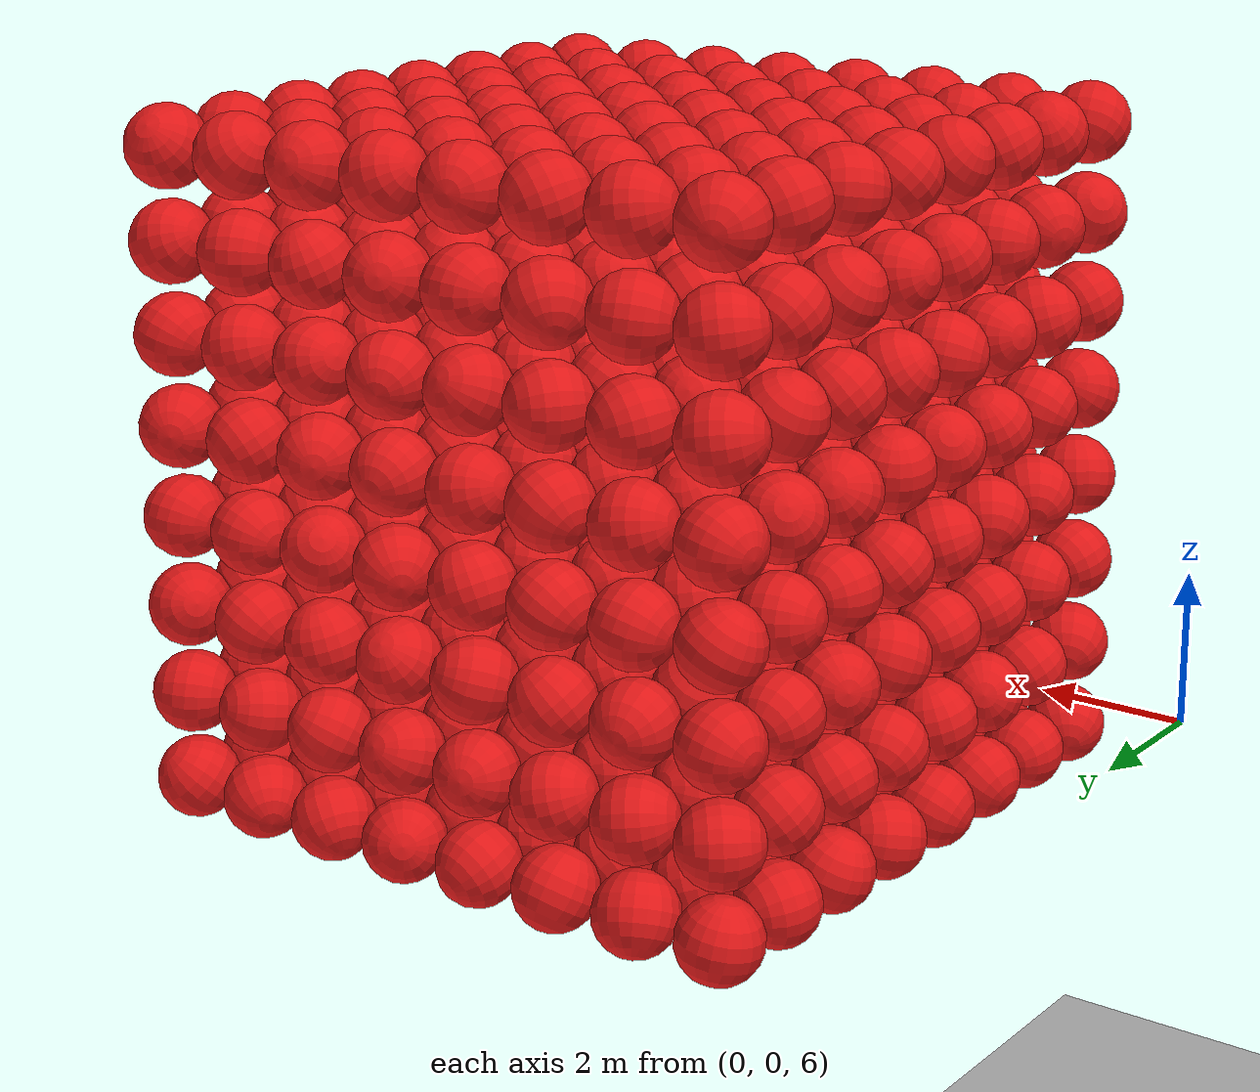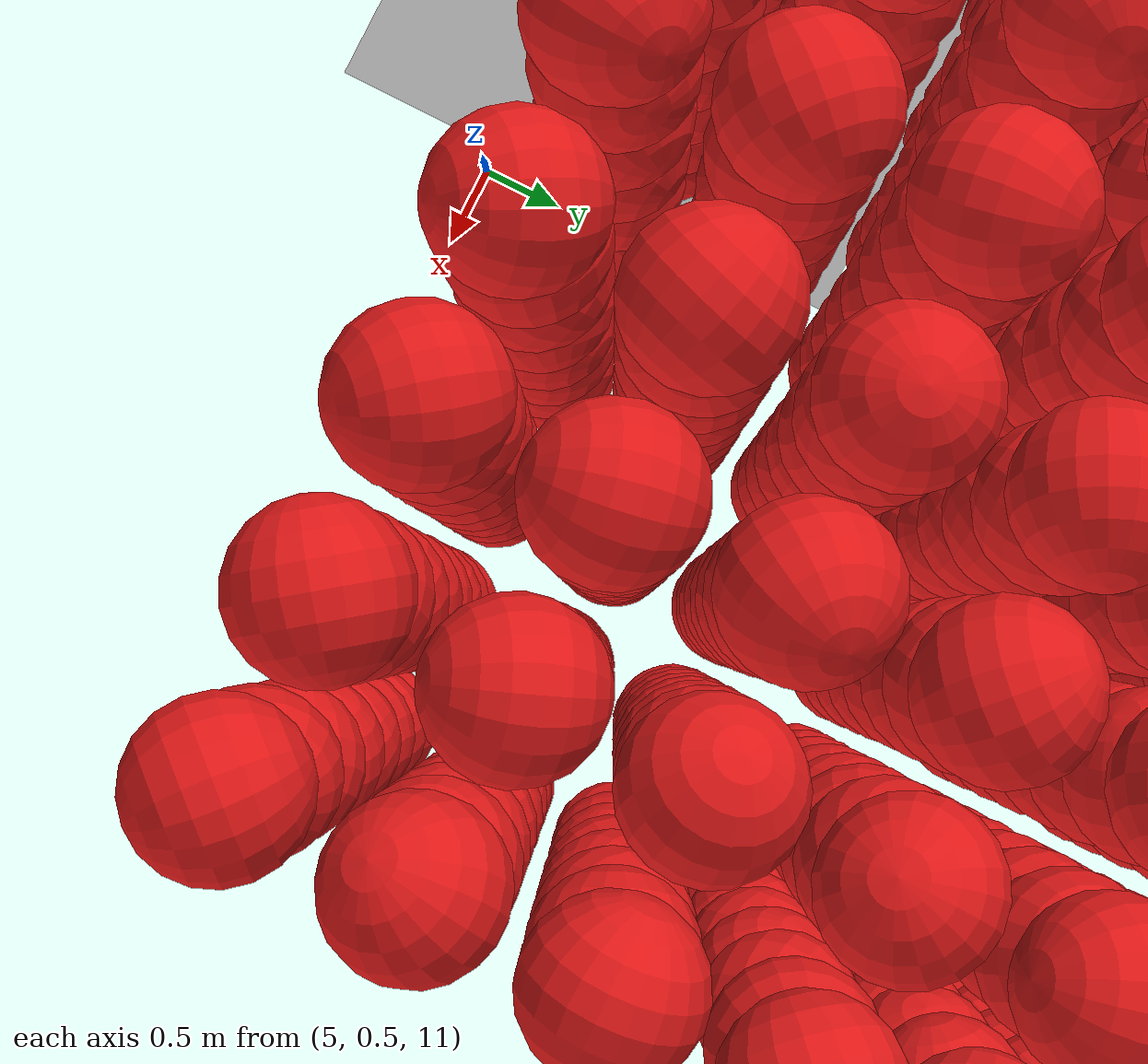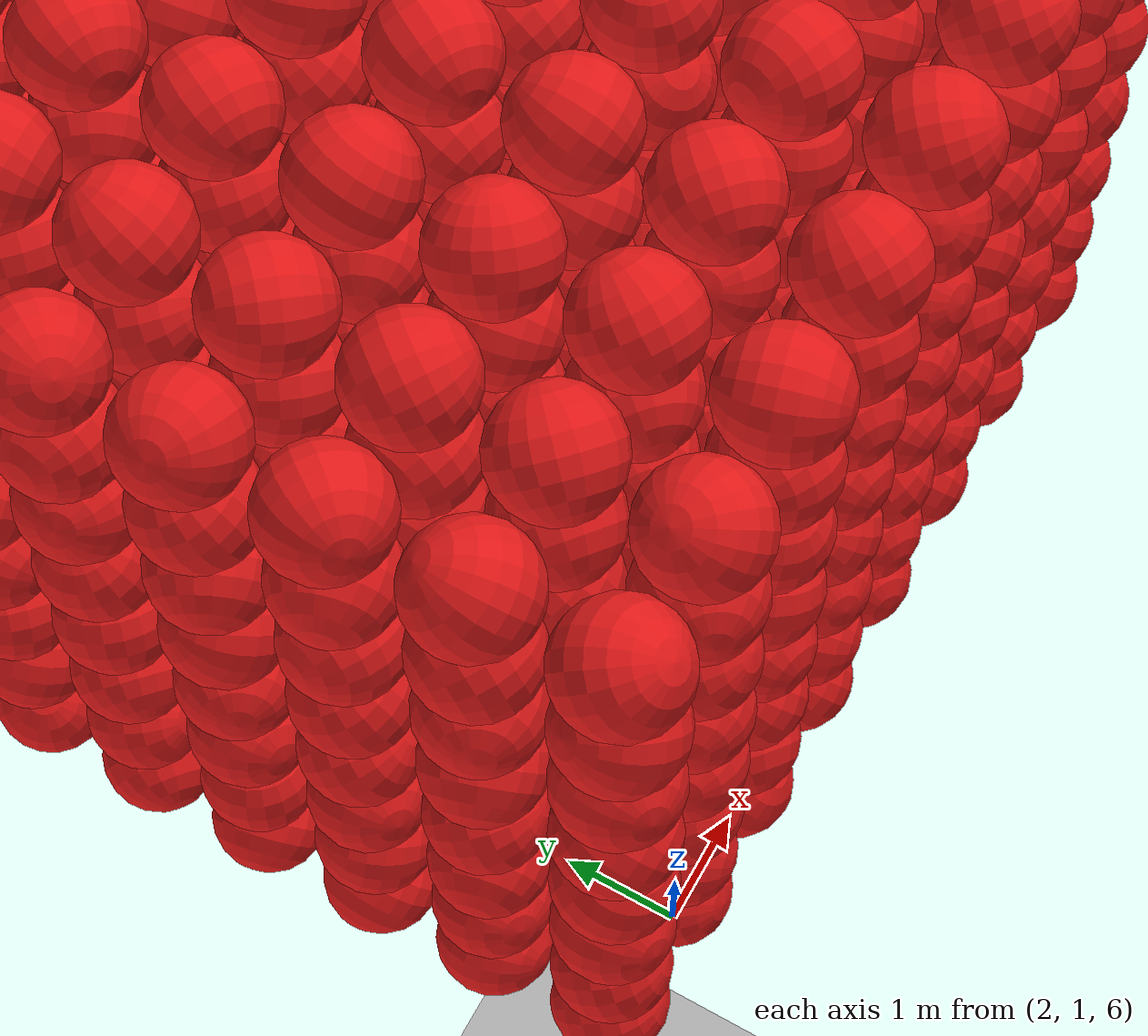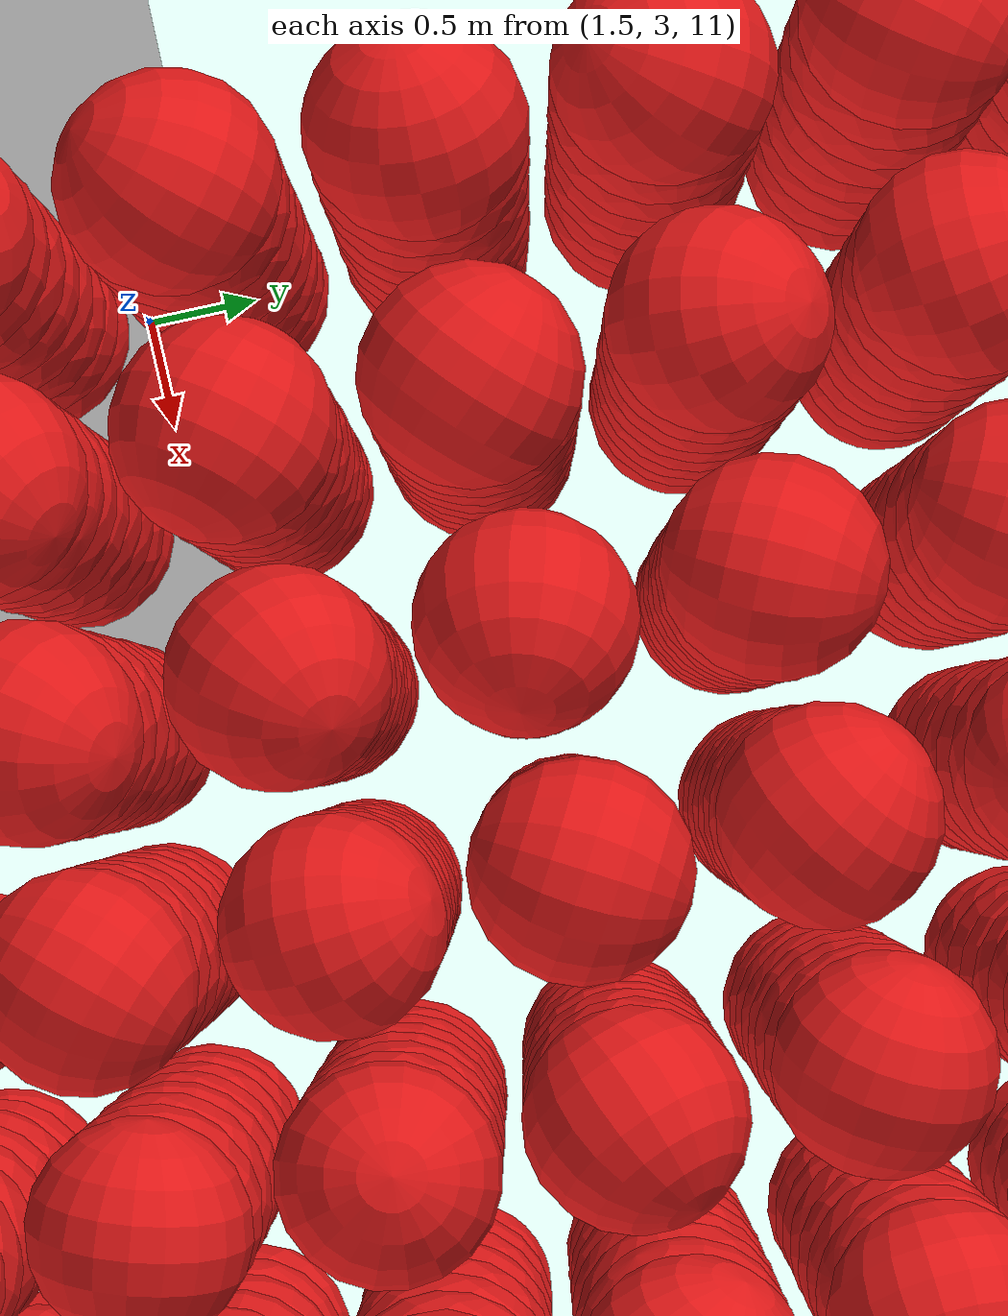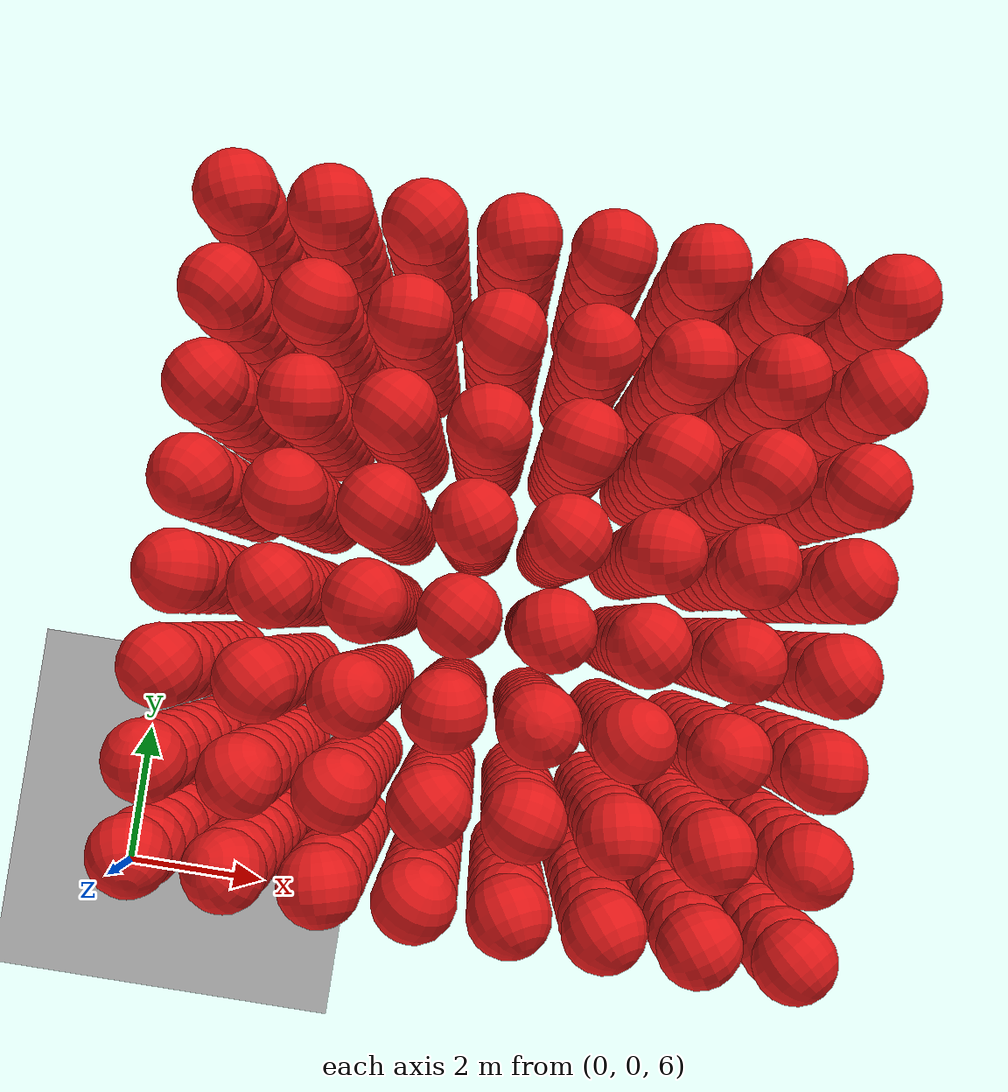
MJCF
<mujoco model="Humanoid and 100 objects">
    <compiler angle="degree"/>

    <option timestep="0.01" iterations="50" solver="PGS" jacobian="sparse" cone="elliptic" tolerance="1e-10"/>

    <size njmax="5000" nconmax="2000" nstack="1000000000"/>

    <default>
        <geom solimp=".9 .9 .01"/>

        <default class="object5">
			<geom type="sphere" material="geom" rgba=".9 .1 .1 1" size="0.500000"/>
        </default>
    </default>

    <asset>
        <texture type="skybox" builtin="gradient" width="128" height="128" rgb1=".4 .6 .8" rgb2="0 0 0"/>
        <texture name="texgeom" type="cube" builtin="flat" mark="cross" width="128" height="128"
            rgb1="0.6 0.6 0.6" rgb2="0.6 0.6 0.6" markrgb="1 1 1"/>
        <texture name="texplane" type="2d" builtin="checker" rgb1=".4 .4 .4" rgb2=".6 .6 .6"
            width="512" height="512"/>
        <material name='geom' texture="texgeom" texuniform="true"/>
        <material name='MatPlane' reflectance='0.3' texture="texplane" texrepeat="1 1" texuniform="true"/>
    </asset>

    <visual>
        <quality shadowsize="4096" offsamples="8"/>
        <map znear="0.1" force="0.05"/>
    </visual>

    <statistic extent="4"/>

    <worldbody>
        <light directional="true" diffuse=".8 .8 .8" pos="0 0 10" dir="0 0 -10"/>

        <geom pos="0 0 0" type="plane" size="3 3 .5" rgba=".7 .7 .7 1" material="MatPlane"/>
		<body pos="1.100771 1.100686 6.100868" quat="0.159258 0.249450 -0.769197 -0.566346"> <freejoint/> <geom class="object5"/> </body>
		<body pos="1.100036 1.100445 7.200327" quat="-0.367640 -0.006132 -0.550140 0.749766"> <freejoint/> <geom class="object5"/> </body>
		<body pos="1.100940 1.100591 8.300001" quat="0.510231 0.231554 -0.539531 0.628453"> <freejoint/> <geom class="object5"/> </body>
		<body pos="1.100314 1.100809 9.400461" quat="0.255563 -0.065706 0.153833 -0.952211"> <freejoint/> <geom class="object5"/> </body>
		<body pos="1.100587 1.100155 10.500445" quat="0.062643 -0.063440 0.556322 0.826170"> <freejoint/> <geom class="object5"/> </body>
		<body pos="1.100972 1.100746 11.600200" quat="-0.801789 -0.538472 0.134096 0.221811"> <freejoint/> <geom class="object5"/> </body>
		<body pos="1.100365 1.100637 12.700891" quat="-0.495424 -0.429414 -0.752901 0.057433"> <freejoint/> <geom class="object5"/> </body>
		<body pos="1.100821 1.100300 13.800788" quat="-0.119281 0.095709 0.920569 0.359394"> <freejoint/> <geom class="object5"/> </body>
		<body pos="1.100970 2.200096 6.100898" quat="-0.725108 -0.618573 0.214673 -0.213310"> <freejoint/> <geom class="object5"/> </body>
		<body pos="1.100320 2.200796 7.200302" quat="0.263347 -0.093191 -0.508274 0.814629"> <freejoint/> <geom class="object5"/> </body>
		<body pos="1.100571 2.200071 8.300266" quat="-0.734536 0.134593 -0.664869 -0.017031"> <freejoint/> <geom class="object5"/> </body>
		<body pos="1.100729 2.200955 9.400762" quat="-0.539885 0.563430 0.610006 0.137706"> <freejoint/> <geom class="object5"/> </body>
		<body pos="1.100957 2.200331 10.500901" quat="-0.781809 -0.026163 -0.551619 -0.289494"> <freejoint/> <geom class="object5"/> </body>
		<body pos="1.100171 2.200593 11.600658" quat="-0.191153 -0.564845 -0.573104 -0.562106"> <freejoint/> <geom class="object5"/> </body>
		<body pos="1.100072 2.200016 12.700974" quat="0.337898 0.363211 -0.671613 -0.550307"> <freejoint/> <geom class="object5"/> </body>
		<body pos="1.100261 2.200893 13.800972" quat="0.772995 -0.239708 -0.324950 -0.489312"> <freejoint/> <geom class="object5"/> </body>
		<body pos="1.100743 3.300718 6.100189" quat="-0.117892 -0.810915 0.277451 0.501536"> <freejoint/> <geom class="object5"/> </body>
		<body pos="1.100863 3.300785 7.200433" quat="-0.220091 -0.643025 0.461997 -0.569770"> <freejoint/> <geom class="object5"/> </body>
		<body pos="1.100006 3.300275 8.300943" quat="0.388285 -0.254776 0.795348 0.389545"> <freejoint/> <geom class="object5"/> </body>
		<body pos="1.100608 3.300439 9.400961" quat="0.469703 -0.712033 -0.521308 -0.025005"> <freejoint/> <geom class="object5"/> </body>
		<body pos="1.100581 3.300293 10.500439" quat="-0.168053 -0.599124 0.747904 -0.231188"> <freejoint/> <geom class="object5"/> </body>
		<body pos="1.100837 3.300041 11.600424" quat="-0.577847 -0.253525 0.607287 0.482722"> <freejoint/> <geom class="object5"/> </body>
		<body pos="1.100174 3.300536 12.700295" quat="0.555385 -0.577084 0.396303 -0.448849"> <freejoint/> <geom class="object5"/> </body>
		<body pos="1.100720 3.300232 13.800207" quat="-0.486788 0.817413 -0.202610 0.231999"> <freejoint/> <geom class="object5"/> </body>
		<body pos="1.100047 4.400232 6.100875" quat="-0.066915 -0.834291 -0.058859 0.544074"> <freejoint/> <geom class="object5"/> </body>
		<body pos="1.100872 4.400301 7.200236" quat="0.718795 -0.134940 0.015364 -0.681828"> <freejoint/> <geom class="object5"/> </body>
		<body pos="1.100151 4.400907 8.300993" quat="-0.158626 0.471628 0.655262 0.568363"> <freejoint/> <geom class="object5"/> </body>
		<body pos="1.100841 4.400683 9.400172" quat="-0.442176 -0.110717 -0.800180 -0.389787"> <freejoint/> <geom class="object5"/> </body>
		<body pos="1.100980 4.400313 10.500572" quat="0.237169 0.852855 -0.220808 0.409431"> <freejoint/> <geom class="object5"/> </body>
		<body pos="1.100204 4.400063 11.600622" quat="0.553135 -0.597838 0.210528 -0.540655"> <freejoint/> <geom class="object5"/> </body>
		<body pos="1.100809 4.400365 12.700699" quat="0.231286 0.805322 -0.518652 0.170186"> <freejoint/> <geom class="object5"/> </body>
		<body pos="1.100084 4.400544 13.800846" quat="-0.714070 -0.265291 0.325473 0.560171"> <freejoint/> <geom class="object5"/> </body>
		<body pos="1.100501 5.500995 6.100429" quat="-0.434860 -0.050556 -0.633921 -0.637561"> <freejoint/> <geom class="object5"/> </body>
		<body pos="1.100268 5.500757 7.200609" quat="0.851765 0.498583 0.132917 -0.090801"> <freejoint/> <geom class="object5"/> </body>
		<body pos="1.100287 5.500752 8.300094" quat="-0.806964 0.482055 -0.298410 0.165478"> <freejoint/> <geom class="object5"/> </body>
		<body pos="1.100299 5.500714 9.400360" quat="0.319546 0.724521 -0.608931 -0.046506"> <freejoint/> <geom class="object5"/> </body>
		<body pos="1.100094 5.500725 10.500912" quat="-0.905756 0.043693 0.115262 0.405478"> <freejoint/> <geom class="object5"/> </body>
		<body pos="1.100300 5.500602 11.600199" quat="0.366699 0.464012 -0.094319 -0.800830"> <freejoint/> <geom class="object5"/> </body>
		<body pos="1.100422 5.500596 12.700322" quat="0.465326 -0.530872 -0.350082 0.615702"> <freejoint/> <geom class="object5"/> </body>
		<body pos="1.100655 5.500753 13.800811" quat="-0.720948 -0.136169 0.359999 -0.576275"> <freejoint/> <geom class="object5"/> </body>
		<body pos="1.100633 6.600247 6.100840" quat="0.577645 -0.080516 -0.180568 0.791984"> <freejoint/> <geom class="object5"/> </body>
		<body pos="1.100008 6.600398 7.200488" quat="0.199600 -0.726499 -0.603704 0.260577"> <freejoint/> <geom class="object5"/> </body>
		<body pos="1.100218 6.600119 8.300043" quat="-0.593300 0.019702 0.651533 0.472347"> <freejoint/> <geom class="object5"/> </body>
		<body pos="1.100135 6.600065 9.400672" quat="-0.069114 -0.017798 -0.724491 -0.685580"> <freejoint/> <geom class="object5"/> </body>
		<body pos="1.100909 6.600450 10.500749" quat="-0.524099 -0.691165 -0.487839 0.098103"> <freejoint/> <geom class="object5"/> </body>
		<body pos="1.100662 6.600939 11.600040" quat="-0.598797 -0.110161 -0.310368 -0.730054"> <freejoint/> <geom class="object5"/> </body>
		<body pos="1.100810 6.600400 12.700655" quat="0.120499 -0.895724 0.272842 -0.329719"> <freejoint/> <geom class="object5"/> </body>
		<body pos="1.100266 6.600460 13.800623" quat="0.473247 0.095893 -0.745014 0.460214"> <freejoint/> <geom class="object5"/> </body>
		<body pos="1.100273 7.700823 6.100689" quat="0.153041 -0.166515 -0.639936 0.734393"> <freejoint/> <geom class="object5"/> </body>
		<body pos="1.100661 7.700229 7.200092" quat="-0.465617 0.723660 -0.508096 -0.036810"> <freejoint/> <geom class="object5"/> </body>
		<body pos="1.100909 7.700194 8.300448" quat="0.364861 0.291805 0.513769 -0.719561"> <freejoint/> <geom class="object5"/> </body>
		<body pos="1.100424 7.700799 9.400932" quat="-0.107453 -0.687342 -0.215142 -0.685367"> <freejoint/> <geom class="object5"/> </body>
		<body pos="1.100275 7.700139 10.500167" quat="-0.008766 -0.598771 0.618211 -0.509129"> <freejoint/> <geom class="object5"/> </body>
		<body pos="1.100160 7.700718 11.600675" quat="-0.211910 -0.613415 -0.736550 -0.190553"> <freejoint/> <geom class="object5"/> </body>
		<body pos="1.100788 7.700447 12.700100" quat="0.874372 0.455882 -0.136191 0.095383"> <freejoint/> <geom class="object5"/> </body>
		<body pos="1.100527 7.700630 13.800647" quat="-0.576296 0.564258 -0.567431 -0.165886"> <freejoint/> <geom class="object5"/> </body>
		<body pos="1.100236 8.800272 6.100009" quat="0.993924 0.046924 -0.083255 0.054606"> <freejoint/> <geom class="object5"/> </body>
		<body pos="1.100337 8.800332 7.200988" quat="-0.062316 0.585295 0.402964 0.700833"> <freejoint/> <geom class="object5"/> </body>
		<body pos="1.100273 8.800284 8.300717" quat="-0.435084 0.460387 -0.455740 0.625338"> <freejoint/> <geom class="object5"/> </body>
		<body pos="1.100723 8.800134 9.400853" quat="0.955490 0.142064 -0.223940 -0.129255"> <freejoint/> <geom class="object5"/> </body>
		<body pos="1.100702 8.800260 10.500029" quat="0.512343 0.567474 0.319648 0.559734"> <freejoint/> <geom class="object5"/> </body>
		<body pos="1.100488 8.800128 11.600464" quat="0.446291 0.318987 0.688006 0.475100"> <freejoint/> <geom class="object5"/> </body>
		<body pos="1.100617 8.800275 12.700336" quat="0.508734 -0.172921 -0.635917 0.553984"> <freejoint/> <geom class="object5"/> </body>
		<body pos="1.100435 8.800172 13.800004" quat="0.627670 -0.536351 -0.509970 -0.241432"> <freejoint/> <geom class="object5"/> </body>
		<body pos="2.200516 1.100300 6.100478" quat="-0.735963 -0.489741 -0.292807 0.364386"> <freejoint/> <geom class="object5"/> </body>
		<body pos="2.200581 1.100701 7.200805" quat="0.587666 -0.638243 0.262563 0.422321"> <freejoint/> <geom class="object5"/> </body>
		<body pos="2.200702 1.100605 8.300038" quat="-0.647206 -0.359468 0.303240 -0.599960"> <freejoint/> <geom class="object5"/> </body>
		<body pos="2.200077 1.100981 9.400207" quat="0.868575 0.198375 -0.452971 0.032277"> <freejoint/> <geom class="object5"/> </body>
		<body pos="2.200713 1.100260 10.500115" quat="0.085105 -0.481643 -0.321825 0.810682"> <freejoint/> <geom class="object5"/> </body>
		<body pos="2.200309 1.100946 11.600411" quat="-0.612635 -0.237628 -0.431380 0.618160"> <freejoint/> <geom class="object5"/> </body>
		<body pos="2.200450 1.100545 12.700262" quat="0.594612 -0.616991 0.502937 -0.113196"> <freejoint/> <geom class="object5"/> </body>
		<body pos="2.200920 1.100528 13.800871" quat="-0.320758 -0.217590 0.213396 0.896789"> <freejoint/> <geom class="object5"/> </body>
		<body pos="2.200133 2.200042 6.100401" quat="0.199630 0.875382 -0.430150 0.093945"> <freejoint/> <geom class="object5"/> </body>
		<body pos="2.200782 2.200327 7.200095" quat="-0.091435 -0.738351 0.274991 -0.608980"> <freejoint/> <geom class="object5"/> </body>
		<body pos="2.200200 2.200530 8.300627" quat="-0.291468 0.245466 0.798722 0.465657"> <freejoint/> <geom class="object5"/> </body>
		<body pos="2.200393 2.200572 9.400250" quat="0.420082 -0.289490 -0.778581 -0.365429"> <freejoint/> <geom class="object5"/> </body>
		<body pos="2.200300 2.200023 10.500176" quat="0.624347 0.269772 0.616768 -0.396246"> <freejoint/> <geom class="object5"/> </body>
		<body pos="2.200896 2.200209 11.600964" quat="-0.190875 -0.602748 0.709587 -0.311045"> <freejoint/> <geom class="object5"/> </body>
		<body pos="2.200502 2.200748 12.700832" quat="-0.188291 -0.719705 -0.418602 0.520906"> <freejoint/> <geom class="object5"/> </body>
		<body pos="2.200937 2.200568 13.800938" quat="0.150919 0.757249 0.407137 -0.487890"> <freejoint/> <geom class="object5"/> </body>
		<body pos="2.200517 3.300640 6.100869" quat="0.150951 0.753366 -0.559102 -0.311541"> <freejoint/> <geom class="object5"/> </body>
		<body pos="2.200477 3.300130 7.200228" quat="-0.642895 0.346749 -0.351183 0.585766"> <freejoint/> <geom class="object5"/> </body>
		<body pos="2.200546 3.300231 8.300687" quat="-0.656909 0.105764 0.719327 -0.199631"> <freejoint/> <geom class="object5"/> </body>
		<body pos="2.200559 3.300927 9.400260" quat="0.519921 -0.508035 0.593993 -0.344608"> <freejoint/> <geom class="object5"/> </body>
		<body pos="2.200849 3.300807 10.500189" quat="0.702667 -0.361601 0.408989 0.456324"> <freejoint/> <geom class="object5"/> </body>
		<body pos="2.200498 3.300916 11.600101" quat="-0.493370 0.485433 -0.652118 0.309329"> <freejoint/> <geom class="object5"/> </body>
		<body pos="2.200817 3.300116 12.700489" quat="-0.305333 0.548195 -0.429750 0.649283"> <freejoint/> <geom class="object5"/> </body>
		<body pos="2.200173 3.300864 13.800926" quat="-0.420152 -0.611598 0.065900 -0.667141"> <freejoint/> <geom class="object5"/> </body>
		<body pos="2.200828 4.400909 6.100705" quat="-0.394691 0.137215 0.674914 0.608179"> <freejoint/> <geom class="object5"/> </body>
		<body pos="2.200606 4.400792 7.200836" quat="0.106412 -0.883459 -0.440088 -0.120409"> <freejoint/> <geom class="object5"/> </body>
		<body pos="2.200431 4.400875 8.300068" quat="-0.322570 -0.650685 -0.511711 0.459031"> <freejoint/> <geom class="object5"/> </body>
		<body pos="2.200288 4.400237 9.400140" quat="-0.593988 0.675401 -0.258999 0.352040"> <freejoint/> <geom class="object5"/> </body>
		<body pos="2.200936 4.400426 10.500605" quat="0.857072 -0.247035 0.300145 -0.338104"> <freejoint/> <geom class="object5"/> </body>
		<body pos="2.200886 4.400296 11.600295" quat="0.589800 -0.010309 -0.424310 -0.687016"> <freejoint/> <geom class="object5"/> </body>
		<body pos="2.200170 4.400302 12.700961" quat="0.587855 0.359059 0.706116 -0.164022"> <freejoint/> <geom class="object5"/> </body>
		<body pos="2.200704 4.400481 13.800821" quat="-0.079468 0.456898 -0.623334 0.629590"> <freejoint/> <geom class="object5"/> </body>
		<body pos="2.200275 5.500034 6.100152" quat="-0.038611 0.735829 -0.409849 0.537670"> <freejoint/> <geom class="object5"/> </body>
		<body pos="2.200170 5.500731 7.200247" quat="-0.566911 0.478449 0.252914 0.621074"> <freejoint/> <geom class="object5"/> </body>
		<body pos="2.200985 5.500535 8.300906" quat="-0.032478 0.541967 -0.662245 -0.516381"> <freejoint/> <geom class="object5"/> </body>
		<body pos="2.200741 5.500391 9.400394" quat="0.152480 -0.712805 -0.168171 -0.663609"> <freejoint/> <geom class="object5"/> </body>
		<body pos="2.200690 5.500520 10.500076" quat="-0.272495 -0.202865 0.463106 -0.818612"> <freejoint/> <geom class="object5"/> </body>
		<body pos="2.200081 5.500468 11.600729" quat="0.203759 0.716112 -0.441934 -0.500360"> <freejoint/> <geom class="object5"/> </body>
		<body pos="2.200236 5.500810 12.700702" quat="0.811806 0.452571 0.345480 -0.129593"> <freejoint/> <geom class="object5"/> </body>
		<body pos="2.200563 5.500990 13.800957" quat="-0.414238 -0.874628 -0.210495 0.138290"> <freejoint/> <geom class="object5"/> </body>
		<body pos="2.200030 6.600867 6.100894" quat="-0.006745 -0.697907 0.531982 0.479453"> <freejoint/> <geom class="object5"/> </body>
		<body pos="2.200461 6.600171 7.200794" quat="0.457287 -0.420781 0.517519 -0.588222"> <freejoint/> <geom class="object5"/> </body>
		<body pos="2.200439 6.600011 8.300235" quat="0.508349 0.476863 -0.576858 -0.425931"> <freejoint/> <geom class="object5"/> </body>
		<body pos="2.200093 6.600042 9.400759" quat="-0.340901 0.042479 0.879650 0.328935"> <freejoint/> <geom class="object5"/> </body>
		<body pos="2.200473 6.600649 10.500666" quat="-0.654223 0.739166 0.006752 -0.159937"> <freejoint/> <geom class="object5"/> </body>
		<body pos="2.200709 6.600555 11.600255" quat="-0.892585 0.187221 0.366116 0.184933"> <freejoint/> <geom class="object5"/> </body>
		<body pos="2.200534 6.600473 12.700324" quat="-0.112456 0.431642 0.808969 -0.382895"> <freejoint/> <geom class="object5"/> </body>
		<body pos="2.200792 6.600135 13.800036" quat="-0.101788 0.139193 -0.594809 -0.785154"> <freejoint/> <geom class="object5"/> </body>
		<body pos="2.200677 7.700354 6.100510" quat="0.554215 0.271243 0.017394 0.786746"> <freejoint/> <geom class="object5"/> </body>
		<body pos="2.200685 7.700319 7.200832" quat="0.261485 0.141567 -0.781945 0.547857"> <freejoint/> <geom class="object5"/> </body>
		<body pos="2.200114 7.700840 8.300337" quat="-0.146677 0.610655 -0.745047 0.224703"> <freejoint/> <geom class="object5"/> </body>
		<body pos="2.200931 7.700636 9.400048" quat="0.506255 -0.619949 0.487254 -0.349217"> <freejoint/> <geom class="object5"/> </body>
		<body pos="2.200542 7.700222 10.500905" quat="-0.192956 -0.642659 -0.715726 0.193630"> <freejoint/> <geom class="object5"/> </body>
		<body pos="2.200937 7.700320 11.600745" quat="-0.473735 -0.843110 0.031604 -0.252471"> <freejoint/> <geom class="object5"/> </body>
		<body pos="2.200979 7.700292 12.700592" quat="0.268389 0.435762 0.229113 -0.828001"> <freejoint/> <geom class="object5"/> </body>
		<body pos="2.200152 7.700733 13.800040" quat="0.459694 -0.142627 0.502961 0.717892"> <freejoint/> <geom class="object5"/> </body>
		<body pos="2.200422 8.800054 6.100787" quat="0.540174 0.036624 0.281082 -0.792378"> <freejoint/> <geom class="object5"/> </body>
		<body pos="2.200747 8.800337 7.200883" quat="-0.259636 0.462030 0.475718 -0.702004"> <freejoint/> <geom class="object5"/> </body>
		<body pos="2.200403 8.800965 8.300414" quat="-0.333263 0.268166 0.704031 0.566889"> <freejoint/> <geom class="object5"/> </body>
		<body pos="2.200538 8.800742 9.400740" quat="-0.096583 0.613049 -0.009561 0.784061"> <freejoint/> <geom class="object5"/> </body>
		<body pos="2.200798 8.800133 10.500238" quat="-0.641038 0.058753 -0.763342 -0.054112"> <freejoint/> <geom class="object5"/> </body>
		<body pos="2.200983 8.800682 11.600871" quat="-0.006331 -0.354734 -0.529552 0.770518"> <freejoint/> <geom class="object5"/> </body>
		<body pos="2.200756 8.800950 12.700671" quat="-0.424956 -0.284469 -0.598009 -0.617151"> <freejoint/> <geom class="object5"/> </body>
		<body pos="2.200280 8.800170 13.800677" quat="0.613988 -0.225830 -0.610057 0.447047"> <freejoint/> <geom class="object5"/> </body>
		<body pos="3.300468 1.100687 6.100683" quat="-0.351358 0.712619 0.596719 0.112459"> <freejoint/> <geom class="object5"/> </body>
		<body pos="3.300191 1.100512 7.200748" quat="-0.145104 0.429810 0.337485 0.824811"> <freejoint/> <geom class="object5"/> </body>
		<body pos="3.300308 1.100342 8.300387" quat="-0.920978 0.259576 0.126829 -0.261407"> <freejoint/> <geom class="object5"/> </body>
		<body pos="3.300421 1.100462 9.400314" quat="-0.367873 -0.515009 -0.490832 0.598765"> <freejoint/> <geom class="object5"/> </body>
		<body pos="3.300492 1.100748 10.500311" quat="-0.901575 0.211746 -0.260836 0.272562"> <freejoint/> <geom class="object5"/> </body>
		<body pos="3.300846 1.100101 11.600588" quat="0.172859 0.045750 -0.095261 0.979261"> <freejoint/> <geom class="object5"/> </body>
		<body pos="3.300182 1.100559 12.700626" quat="-0.776280 0.235052 0.558682 -0.173248"> <freejoint/> <geom class="object5"/> </body>
		<body pos="3.300437 1.100085 13.800581" quat="0.533283 -0.420525 -0.581647 -0.447721"> <freejoint/> <geom class="object5"/> </body>
		<body pos="3.300668 2.200732 6.100631" quat="-0.130526 -0.762115 0.580776 0.254644"> <freejoint/> <geom class="object5"/> </body>
		<body pos="3.300664 2.200125 7.200674" quat="0.275210 0.656494 0.501879 -0.491317"> <freejoint/> <geom class="object5"/> </body>
		<body pos="3.300949 2.200200 8.300218" quat="-0.843328 -0.342105 -0.386986 0.148337"> <freejoint/> <geom class="object5"/> </body>
		<body pos="3.300397 2.200186 9.400393" quat="-0.556931 0.535806 -0.564738 0.289499"> <freejoint/> <geom class="object5"/> </body>
		<body pos="3.300750 2.200015 10.500142" quat="-0.633861 0.416901 -0.611591 0.224432"> <freejoint/> <geom class="object5"/> </body>
		<body pos="3.300456 2.200803 11.600358" quat="-0.800756 -0.474739 0.355811 0.082529"> <freejoint/> <geom class="object5"/> </body>
		<body pos="3.300870 2.200739 12.700103" quat="0.637042 0.322569 -0.656918 0.242045"> <freejoint/> <geom class="object5"/> </body>
		<body pos="3.300486 2.200035 13.800114" quat="-0.677883 0.172642 -0.426759 -0.573190"> <freejoint/> <geom class="object5"/> </body>
		<body pos="3.300530 3.300930 6.100617" quat="0.297814 -0.416509 -0.459766 -0.725564"> <freejoint/> <geom class="object5"/> </body>
		<body pos="3.300663 3.300507 7.200486" quat="0.522532 0.672518 0.375165 -0.365966"> <freejoint/> <geom class="object5"/> </body>
		<body pos="3.300676 3.300759 8.300586" quat="0.440213 0.582740 0.187814 -0.656774"> <freejoint/> <geom class="object5"/> </body>
		<body pos="3.300184 3.300027 9.400935" quat="-0.052055 0.987921 -0.144659 -0.019407"> <freejoint/> <geom class="object5"/> </body>
		<body pos="3.300426 3.300892 10.500874" quat="0.323848 -0.505218 -0.506679 -0.618994"> <freejoint/> <geom class="object5"/> </body>
		<body pos="3.300704 3.300775 11.600823" quat="0.598756 -0.481503 0.587630 0.253647"> <freejoint/> <geom class="object5"/> </body>
		<body pos="3.300232 3.300381 12.700453" quat="0.002128 0.154310 -0.588977 -0.793278"> <freejoint/> <geom class="object5"/> </body>
		<body pos="3.300704 3.300934 13.800594" quat="0.321076 0.823397 -0.439261 -0.161173"> <freejoint/> <geom class="object5"/> </body>
		<body pos="3.300509 4.400929 6.100451" quat="0.284173 -0.084023 0.111189 -0.948590"> <freejoint/> <geom class="object5"/> </body>
		<body pos="3.300802 4.400672 7.200200" quat="-0.840901 0.455893 0.116953 0.267151"> <freejoint/> <geom class="object5"/> </body>
		<body pos="3.300635 4.400734 8.300887" quat="0.353815 -0.808942 0.455809 -0.112542"> <freejoint/> <geom class="object5"/> </body>
		<body pos="3.300641 4.400649 9.400678" quat="-0.587078 -0.367342 -0.441825 0.570254"> <freejoint/> <geom class="object5"/> </body>
		<body pos="3.300515 4.400673 10.500668" quat="-0.611456 -0.401649 -0.315285 0.604480"> <freejoint/> <geom class="object5"/> </body>
		<body pos="3.300229 4.400249 11.600676" quat="0.310411 0.425775 0.704695 0.475148"> <freejoint/> <geom class="object5"/> </body>
		<body pos="3.300019 4.400584 12.700921" quat="-0.611672 0.081733 0.645349 -0.450224"> <freejoint/> <geom class="object5"/> </body>
		<body pos="3.300525 4.400127 13.800749" quat="-0.290047 -0.489578 0.751827 0.333078"> <freejoint/> <geom class="object5"/> </body>
		<body pos="3.300826 5.500683 6.100689" quat="0.096981 -0.977312 -0.021938 0.187015"> <freejoint/> <geom class="object5"/> </body>
		<body pos="3.300828 5.500203 7.200528" quat="0.757086 -0.356382 0.117457 0.534805"> <freejoint/> <geom class="object5"/> </body>
		<body pos="3.300203 5.500644 8.300000" quat="0.020780 0.110121 -0.777408 0.618933"> <freejoint/> <geom class="object5"/> </body>
		<body pos="3.300833 5.500775 9.400788" quat="-0.298076 -0.820108 -0.348481 0.342249"> <freejoint/> <geom class="object5"/> </body>
		<body pos="3.300932 5.500093 10.500739" quat="-0.647147 0.374201 -0.053128 -0.662081"> <freejoint/> <geom class="object5"/> </body>
		<body pos="3.300842 5.500165 11.600115" quat="-0.635077 -0.516019 0.294937 0.493370"> <freejoint/> <geom class="object5"/> </body>
		<body pos="3.300988 5.500993 12.700758" quat="-0.383000 0.773037 -0.151398 -0.482498"> <freejoint/> <geom class="object5"/> </body>
		<body pos="3.300629 5.500015 13.800043" quat="-0.648174 -0.607218 0.444682 -0.115819"> <freejoint/> <geom class="object5"/> </body>
		<body pos="3.300845 6.600390 6.100838" quat="0.577895 0.195086 -0.789606 0.067091"> <freejoint/> <geom class="object5"/> </body>
		<body pos="3.300463 6.600380 7.200093" quat="-0.506990 -0.345558 -0.262884 -0.744610"> <freejoint/> <geom class="object5"/> </body>
		<body pos="3.300317 6.600281 8.300820" quat="-0.291730 0.687252 -0.428552 0.508844"> <freejoint/> <geom class="object5"/> </body>
		<body pos="3.300609 6.600018 9.400702" quat="-0.750999 0.285192 0.586072 -0.105759"> <freejoint/> <geom class="object5"/> </body>
		<body pos="3.300631 6.600586 10.500227" quat="0.483346 -0.360595 0.720593 -0.342191"> <freejoint/> <geom class="object5"/> </body>
		<body pos="3.300536 6.600334 11.600237" quat="0.067282 -0.583466 -0.539638 -0.603184"> <freejoint/> <geom class="object5"/> </body>
		<body pos="3.300311 6.600813 12.700514" quat="0.532392 0.698019 -0.251827 -0.407322"> <freejoint/> <geom class="object5"/> </body>
		<body pos="3.300518 6.600353 13.800859" quat="-0.499600 0.715575 0.172380 0.456769"> <freejoint/> <geom class="object5"/> </body>
		<body pos="3.300344 7.700009 6.100192" quat="0.013987 -0.900711 0.094739 -0.423731"> <freejoint/> <geom class="object5"/> </body>
		<body pos="3.300696 7.700881 7.200025" quat="-0.256010 -0.126711 -0.677114 -0.678174"> <freejoint/> <geom class="object5"/> </body>
		<body pos="3.300072 7.700900 8.300969" quat="-0.296155 -0.507923 0.145263 0.795741"> <freejoint/> <geom class="object5"/> </body>
		<body pos="3.300798 7.700863 9.400798" quat="-0.528071 0.449204 -0.515677 -0.503423"> <freejoint/> <geom class="object5"/> </body>
		<body pos="3.300711 7.700538 10.500525" quat="0.003506 -0.679815 -0.422544 -0.599413"> <freejoint/> <geom class="object5"/> </body>
		<body pos="3.300990 7.700071 11.600060" quat="0.354936 -0.342558 -0.816043 0.301245"> <freejoint/> <geom class="object5"/> </body>
		<body pos="3.300746 7.700805 12.700269" quat="-0.210206 -0.312644 0.344321 0.859948"> <freejoint/> <geom class="object5"/> </body>
		<body pos="3.300941 7.700131 13.800256" quat="-0.182724 0.741374 -0.238821 0.599951"> <freejoint/> <geom class="object5"/> </body>
		<body pos="3.300237 8.800220 6.100991" quat="0.915589 0.280533 0.008384 -0.287971"> <freejoint/> <geom class="object5"/> </body>
		<body pos="3.300768 8.800784 7.200029" quat="-0.769527 -0.303611 0.515277 0.223915"> <freejoint/> <geom class="object5"/> </body>
		<body pos="3.300983 8.800158 8.300617" quat="-0.319259 -0.692521 0.628944 0.151384"> <freejoint/> <geom class="object5"/> </body>
		<body pos="3.300303 8.800168 9.400340" quat="-0.739032 0.262242 -0.436896 0.440661"> <freejoint/> <geom class="object5"/> </body>
		<body pos="3.300299 8.800419 10.500056" quat="-0.627504 -0.419215 -0.306426 -0.580172"> <freejoint/> <geom class="object5"/> </body>
		<body pos="3.300333 8.800050 11.600101" quat="-0.684883 0.647103 -0.301068 0.146803"> <freejoint/> <geom class="object5"/> </body>
		<body pos="3.300378 8.800952 12.700742" quat="0.849910 0.217138 0.416355 -0.239067"> <freejoint/> <geom class="object5"/> </body>
		<body pos="3.300223 8.800131 13.800172" quat="0.589459 -0.625639 0.510111 0.030007"> <freejoint/> <geom class="object5"/> </body>
		<body pos="4.400808 1.100448 6.100347" quat="0.524934 -0.285354 0.115554 0.793514"> <freejoint/> <geom class="object5"/> </body>
		<body pos="4.400840 1.100244 7.200436" quat="0.497088 -0.525447 0.390275 0.569644"> <freejoint/> <geom class="object5"/> </body>
		<body pos="4.400502 1.100570 8.300851" quat="0.829447 0.496689 -0.255550 0.003260"> <freejoint/> <geom class="object5"/> </body>
		<body pos="4.400255 1.100510 9.400079" quat="-0.698460 0.212302 0.183860 -0.658238"> <freejoint/> <geom class="object5"/> </body>
		<body pos="4.400610 1.100545 10.500856" quat="0.220095 -0.352250 -0.606576 -0.677896"> <freejoint/> <geom class="object5"/> </body>
		<body pos="4.400622 1.100699 11.600275" quat="-0.125957 -0.216589 -0.674480 -0.694478"> <freejoint/> <geom class="object5"/> </body>
		<body pos="4.400121 1.100678 12.700219" quat="-0.434401 -0.812461 0.375523 0.100919"> <freejoint/> <geom class="object5"/> </body>
		<body pos="4.400552 1.100742 13.800825" quat="-0.199688 -0.681933 -0.569920 0.412654"> <freejoint/> <geom class="object5"/> </body>
		<body pos="4.400670 2.200060 6.100384" quat="-0.019622 0.613831 -0.788529 -0.032389"> <freejoint/> <geom class="object5"/> </body>
		<body pos="4.400072 2.200787 7.200394" quat="-0.339073 -0.539035 -0.541043 0.549311"> <freejoint/> <geom class="object5"/> </body>
		<body pos="4.400205 2.200957 8.300340" quat="0.693881 -0.236622 -0.658597 0.169671"> <freejoint/> <geom class="object5"/> </body>
		<body pos="4.400556 2.200906 9.400201" quat="0.432823 -0.229100 0.710331 0.505577"> <freejoint/> <geom class="object5"/> </body>
		<body pos="4.400712 2.200215 10.500015" quat="-0.480692 0.060458 -0.649102 0.586469"> <freejoint/> <geom class="object5"/> </body>
		<body pos="4.400911 2.200334 11.600469" quat="-0.852963 -0.324456 -0.025357 -0.408093"> <freejoint/> <geom class="object5"/> </body>
		<body pos="4.400683 2.200911 12.700571" quat="-0.352054 0.642655 -0.653579 0.189437"> <freejoint/> <geom class="object5"/> </body>
		<body pos="4.400948 2.200516 13.800957" quat="-0.414037 0.049017 0.746776 -0.518167"> <freejoint/> <geom class="object5"/> </body>
		<body pos="4.400827 3.300138 6.100438" quat="0.850719 0.463150 -0.006750 0.248442"> <freejoint/> <geom class="object5"/> </body>
		<body pos="4.400078 3.300241 7.200026" quat="0.488725 -0.684313 0.071114 -0.536475"> <freejoint/> <geom class="object5"/> </body>
		<body pos="4.400588 3.300622 8.300747" quat="-0.283835 0.621966 0.421508 -0.595757"> <freejoint/> <geom class="object5"/> </body>
		<body pos="4.400281 3.300908 9.400111" quat="0.496866 -0.681852 0.459363 0.277828"> <freejoint/> <geom class="object5"/> </body>
		<body pos="4.400773 3.300932 10.500177" quat="-0.681514 0.474124 -0.038094 -0.556141"> <freejoint/> <geom class="object5"/> </body>
		<body pos="4.400089 3.300115 11.600168" quat="0.744394 -0.337131 0.156003 0.554872"> <freejoint/> <geom class="object5"/> </body>
		<body pos="4.400245 3.300727 12.700401" quat="-0.407397 0.330821 -0.232683 -0.818806"> <freejoint/> <geom class="object5"/> </body>
		<body pos="4.400979 3.300518 13.800508" quat="-0.315372 -0.545622 0.654059 -0.418382"> <freejoint/> <geom class="object5"/> </body>
		<body pos="4.400539 4.400551 6.100963" quat="-0.600238 -0.610287 -0.494962 0.149256"> <freejoint/> <geom class="object5"/> </body>
		<body pos="4.400378 4.400246 7.200676" quat="-0.455051 0.879744 -0.004620 -0.137690"> <freejoint/> <geom class="object5"/> </body>
		<body pos="4.400568 4.400613 8.300807" quat="0.558826 -0.499005 -0.602911 -0.274238"> <freejoint/> <geom class="object5"/> </body>
		<body pos="4.400607 4.400379 9.400926" quat="-0.638142 0.711652 0.240511 0.168760"> <freejoint/> <geom class="object5"/> </body>
		<body pos="4.400148 4.400029 10.500572" quat="-0.736410 0.331425 -0.448036 -0.383565"> <freejoint/> <geom class="object5"/> </body>
		<body pos="4.400959 4.400182 11.600798" quat="-0.637570 -0.264534 0.647461 -0.322987"> <freejoint/> <geom class="object5"/> </body>
		<body pos="4.400122 4.400607 12.700645" quat="0.498100 0.528570 -0.594411 0.345232"> <freejoint/> <geom class="object5"/> </body>
		<body pos="4.400859 4.400482 13.800075" quat="-0.698403 -0.511559 0.474875 -0.158220"> <freejoint/> <geom class="object5"/> </body>
		<body pos="4.400827 5.500148 6.100733" quat="-0.520844 0.503471 0.067491 0.686064"> <freejoint/> <geom class="object5"/> </body>
		<body pos="4.400075 5.500934 7.200359" quat="-0.657920 0.707846 0.227049 -0.120599"> <freejoint/> <geom class="object5"/> </body>
		<body pos="4.400596 5.500347 8.300218" quat="-0.659067 -0.494237 -0.180565 0.537361"> <freejoint/> <geom class="object5"/> </body>
		<body pos="4.400441 5.500638 9.400388" quat="0.481346 0.380167 -0.534477 -0.581475"> <freejoint/> <geom class="object5"/> </body>
		<body pos="4.400660 5.500378 10.500108" quat="0.269654 0.264840 0.896503 0.231149"> <freejoint/> <geom class="object5"/> </body>
		<body pos="4.400485 5.500577 11.600982" quat="0.026300 -0.214295 0.683929 0.696869"> <freejoint/> <geom class="object5"/> </body>
		<body pos="4.400896 5.500742 12.700665" quat="0.606139 -0.166452 -0.260697 -0.732753"> <freejoint/> <geom class="object5"/> </body>
		<body pos="4.400882 5.500942 13.800949" quat="-0.577694 -0.648838 -0.493612 0.040328"> <freejoint/> <geom class="object5"/> </body>
		<body pos="4.400070 6.600010 6.100092" quat="0.219600 -0.907372 0.323161 0.154978"> <freejoint/> <geom class="object5"/> </body>
		<body pos="4.400074 6.600242 7.200351" quat="-0.567709 0.364127 -0.082618 -0.733685"> <freejoint/> <geom class="object5"/> </body>
		<body pos="4.400682 6.600881 8.300140" quat="0.501076 -0.398374 -0.766660 0.049524"> <freejoint/> <geom class="object5"/> </body>
		<body pos="4.400935 6.600769 9.400405" quat="0.438318 -0.037586 -0.118377 0.890197"> <freejoint/> <geom class="object5"/> </body>
		<body pos="4.400579 6.600784 10.500715" quat="-0.637436 0.343660 -0.189451 -0.663085"> <freejoint/> <geom class="object5"/> </body>
		<body pos="4.400641 6.600498 11.600064" quat="0.037125 -0.292521 0.559761 -0.774416"> <freejoint/> <geom class="object5"/> </body>
		<body pos="4.400203 6.600881 12.700218" quat="-0.466568 -0.399327 0.767957 0.181919"> <freejoint/> <geom class="object5"/> </body>
		<body pos="4.400813 6.600086 13.800192" quat="0.246187 -0.829110 0.461879 0.196562"> <freejoint/> <geom class="object5"/> </body>
		<body pos="4.400798 7.700161 6.100738" quat="0.458604 0.680326 -0.126245 -0.557586"> <freejoint/> <geom class="object5"/> </body>
		<body pos="4.400303 7.700321 7.200442" quat="-0.264421 0.240461 0.840131 -0.407971"> <freejoint/> <geom class="object5"/> </body>
		<body pos="4.400245 7.700921 8.300926" quat="-0.289589 -0.645316 0.427968 -0.562626"> <freejoint/> <geom class="object5"/> </body>
		<body pos="4.400461 7.700440 9.400605" quat="-0.567325 0.150652 -0.559560 -0.585097"> <freejoint/> <geom class="object5"/> </body>
		<body pos="4.400441 7.700271 10.500944" quat="0.082362 -0.270736 -0.947250 -0.150454"> <freejoint/> <geom class="object5"/> </body>
		<body pos="4.400779 7.700169 11.600022" quat="0.431393 0.217319 -0.178403 0.857231"> <freejoint/> <geom class="object5"/> </body>
		<body pos="4.400477 7.700916 12.700497" quat="0.600115 0.285845 0.273201 -0.695354"> <freejoint/> <geom class="object5"/> </body>
		<body pos="4.400540 7.700413 13.800628" quat="0.093489 -0.609870 0.111891 0.778973"> <freejoint/> <geom class="object5"/> </body>
		<body pos="4.400005 8.800125 6.100775" quat="-0.644479 -0.480211 -0.241323 0.543882"> <freejoint/> <geom class="object5"/> </body>
		<body pos="4.400614 8.800016 7.200311" quat="-0.444312 -0.324717 -0.684470 0.478170"> <freejoint/> <geom class="object5"/> </body>
		<body pos="4.400764 8.800721 8.300823" quat="0.394276 -0.565507 -0.172392 -0.703583"> <freejoint/> <geom class="object5"/> </body>
		<body pos="4.400001 8.800007 9.400168" quat="-0.941623 0.041736 -0.218507 0.252704"> <freejoint/> <geom class="object5"/> </body>
		<body pos="4.400277 8.800593 10.500585" quat="-0.469413 -0.522750 -0.580467 -0.411633"> <freejoint/> <geom class="object5"/> </body>
		<body pos="4.400524 8.800841 11.600306" quat="-0.416981 -0.587156 0.602182 -0.344605"> <freejoint/> <geom class="object5"/> </body>
		<body pos="4.400625 8.800207 12.700242" quat="0.364126 -0.514591 0.483440 -0.607366"> <freejoint/> <geom class="object5"/> </body>
		<body pos="4.400980 8.800653 13.800284" quat="0.481921 -0.616599 0.342430 0.519904"> <freejoint/> <geom class="object5"/> </body>
		<body pos="5.500619 1.100721 6.100464" quat="0.342665 -0.652352 -0.405706 -0.540759"> <freejoint/> <geom class="object5"/> </body>
		<body pos="5.500168 1.100942 7.200849" quat="-0.515972 0.228635 -0.656508 -0.500495"> <freejoint/> <geom class="object5"/> </body>
		<body pos="5.500185 1.100645 8.300857" quat="0.700361 -0.011816 0.556676 -0.446617"> <freejoint/> <geom class="object5"/> </body>
		<body pos="5.500967 1.100991 9.400084" quat="-0.351366 -0.478313 -0.586436 0.551227"> <freejoint/> <geom class="object5"/> </body>
		<body pos="5.500365 1.100154 10.500165" quat="0.513978 0.582479 0.022823 -0.629304"> <freejoint/> <geom class="object5"/> </body>
		<body pos="5.500419 1.100122 11.600952" quat="-0.346516 0.593539 0.595859 0.415440"> <freejoint/> <geom class="object5"/> </body>
		<body pos="5.500909 1.100017 12.700959" quat="-0.634477 -0.320962 -0.017750 0.702928"> <freejoint/> <geom class="object5"/> </body>
		<body pos="5.500568 1.100274 13.800129" quat="-0.796200 -0.533839 -0.152657 -0.240370"> <freejoint/> <geom class="object5"/> </body>
		<body pos="5.500425 2.200614 6.100447" quat="-0.585277 -0.558593 -0.121414 0.575050"> <freejoint/> <geom class="object5"/> </body>
		<body pos="5.500543 2.200912 7.200324" quat="-0.398330 0.720614 0.530789 -0.200774"> <freejoint/> <geom class="object5"/> </body>
		<body pos="5.500882 2.200426 8.300466" quat="-0.164052 -0.097882 0.427073 -0.883807"> <freejoint/> <geom class="object5"/> </body>
		<body pos="5.500733 2.200130 9.400497" quat="-0.407715 0.155503 -0.462069 0.772062"> <freejoint/> <geom class="object5"/> </body>
		<body pos="5.500063 2.200183 10.500624" quat="-0.300953 -0.523453 -0.448796 0.658791"> <freejoint/> <geom class="object5"/> </body>
		<body pos="5.500297 2.200237 11.600660" quat="-0.677008 -0.576116 -0.260060 -0.376987"> <freejoint/> <geom class="object5"/> </body>
		<body pos="5.500695 2.200700 12.700852" quat="0.158874 0.189198 0.083177 0.965425"> <freejoint/> <geom class="object5"/> </body>
		<body pos="5.500446 2.200383 13.800595" quat="-0.361582 -0.739804 -0.237507 -0.515304"> <freejoint/> <geom class="object5"/> </body>
		<body pos="5.500643 3.300777 6.100430" quat="0.386192 -0.704763 -0.070029 -0.590983"> <freejoint/> <geom class="object5"/> </body>
		<body pos="5.500827 3.300743 7.200144" quat="-0.719899 0.053586 0.406785 0.559821"> <freejoint/> <geom class="object5"/> </body>
		<body pos="5.500721 3.300888 8.300163" quat="-0.516536 0.660385 -0.065770 -0.541069"> <freejoint/> <geom class="object5"/> </body>
		<body pos="5.500725 3.300884 9.400798" quat="0.758716 0.084165 -0.642441 0.067351"> <freejoint/> <geom class="object5"/> </body>
		<body pos="5.500843 3.300215 10.500717" quat="0.631568 -0.050042 -0.068780 0.770640"> <freejoint/> <geom class="object5"/> </body>
		<body pos="5.500628 3.300806 11.600402" quat="-0.411109 -0.278961 0.504017 -0.706496"> <freejoint/> <geom class="object5"/> </body>
		<body pos="5.500490 3.300121 12.700140" quat="0.870257 0.254820 -0.119378 0.404311"> <freejoint/> <geom class="object5"/> </body>
		<body pos="5.500530 3.300652 13.800778" quat="0.289550 0.005121 -0.035888 -0.956476"> <freejoint/> <geom class="object5"/> </body>
		<body pos="5.500917 4.400433 6.100427" quat="-0.674400 0.014938 0.664355 -0.321860"> <freejoint/> <geom class="object5"/> </body>
		<body pos="5.500743 4.400117 7.200769" quat="0.438848 0.067327 -0.546136 0.710363"> <freejoint/> <geom class="object5"/> </body>
		<body pos="5.500208 4.400020 8.300602" quat="0.400960 -0.116306 0.359668 0.834471"> <freejoint/> <geom class="object5"/> </body>
		<body pos="5.500408 4.400598 9.400426" quat="-0.682772 -0.270912 0.084400 -0.673280"> <freejoint/> <geom class="object5"/> </body>
		<body pos="5.500081 4.400289 10.500677" quat="-0.069816 -0.001276 -0.717567 -0.692981"> <freejoint/> <geom class="object5"/> </body>
		<body pos="5.500338 4.400336 11.600985" quat="0.523015 0.304525 0.795682 0.024710"> <freejoint/> <geom class="object5"/> </body>
		<body pos="5.500376 4.400884 12.700246" quat="-0.598653 0.282588 -0.435420 -0.610056"> <freejoint/> <geom class="object5"/> </body>
		<body pos="5.500277 4.400299 13.800006" quat="-0.432274 0.271008 0.767323 -0.388470"> <freejoint/> <geom class="object5"/> </body>
		<body pos="5.500619 5.500972 6.100492" quat="-0.458934 0.223955 0.100063 -0.853939"> <freejoint/> <geom class="object5"/> </body>
		<body pos="5.500552 5.500149 7.200259" quat="0.074941 0.817942 0.570395 0.002138"> <freejoint/> <geom class="object5"/> </body>
		<body pos="5.500894 5.500951 8.300462" quat="-0.349521 0.701612 -0.006042 0.620918"> <freejoint/> <geom class="object5"/> </body>
		<body pos="5.500213 5.500114 9.400124" quat="0.250776 -0.113802 -0.426273 0.861657"> <freejoint/> <geom class="object5"/> </body>
		<body pos="5.500456 5.500706 10.500930" quat="0.387969 -0.557080 0.564387 0.469690"> <freejoint/> <geom class="object5"/> </body>
		<body pos="5.500639 5.500011 11.600977" quat="-0.710694 -0.622965 0.063873 0.320545"> <freejoint/> <geom class="object5"/> </body>
		<body pos="5.500959 5.500855 12.700477" quat="0.600990 -0.175171 -0.717146 -0.306313"> <freejoint/> <geom class="object5"/> </body>
		<body pos="5.500320 5.500461 13.800488" quat="0.371944 -0.238743 0.794185 -0.417049"> <freejoint/> <geom class="object5"/> </body>
		<body pos="5.500745 6.600909 6.100585" quat="0.519605 -0.566662 0.072522 -0.635331"> <freejoint/> <geom class="object5"/> </body>
		<body pos="5.500153 6.600407 7.200233" quat="0.119146 -0.635628 0.703918 0.293736"> <freejoint/> <geom class="object5"/> </body>
		<body pos="5.500239 6.600064 8.300003" quat="-0.618626 -0.017501 0.231728 -0.750531"> <freejoint/> <geom class="object5"/> </body>
		<body pos="5.500133 6.600314 9.400088" quat="-0.234485 -0.559640 0.335737 -0.720486"> <freejoint/> <geom class="object5"/> </body>
		<body pos="5.500654 6.600193 10.500095" quat="0.720720 0.100331 -0.141882 -0.671093"> <freejoint/> <geom class="object5"/> </body>
		<body pos="5.500553 6.600111 11.600236" quat="-0.596079 -0.283336 -0.253310 0.707280"> <freejoint/> <geom class="object5"/> </body>
		<body pos="5.500888 6.600790 12.700074" quat="-0.160627 -0.206836 -0.174379 0.949215"> <freejoint/> <geom class="object5"/> </body>
		<body pos="5.500238 6.600109 13.800800" quat="-0.535740 0.541352 0.355025 0.542105"> <freejoint/> <geom class="object5"/> </body>
		<body pos="5.500766 7.700608 6.100989" quat="0.157697 -0.010366 -0.622557 -0.766450"> <freejoint/> <geom class="object5"/> </body>
		<body pos="5.500493 7.700711 7.200988" quat="-0.303779 -0.514015 -0.284197 -0.750159"> <freejoint/> <geom class="object5"/> </body>
		<body pos="5.500632 7.700378 8.300887" quat="-0.129414 0.688308 -0.485741 0.523011"> <freejoint/> <geom class="object5"/> </body>
		<body pos="5.500858 7.700427 9.400589" quat="-0.836698 -0.511111 0.192158 0.042172"> <freejoint/> <geom class="object5"/> </body>
		<body pos="5.500914 7.700663 10.500500" quat="0.198023 -0.607629 -0.674546 0.369543"> <freejoint/> <geom class="object5"/> </body>
		<body pos="5.500324 7.700066 11.600923" quat="-0.709628 -0.688000 0.117095 -0.096819"> <freejoint/> <geom class="object5"/> </body>
		<body pos="5.500027 7.700050 12.700239" quat="-0.670959 0.234627 -0.042461 -0.702111"> <freejoint/> <geom class="object5"/> </body>
		<body pos="5.500435 7.700902 13.800566" quat="0.426599 0.889585 0.163151 0.005847"> <freejoint/> <geom class="object5"/> </body>
		<body pos="5.500532 8.800606 6.100764" quat="0.344457 0.761958 -0.221773 0.501584"> <freejoint/> <geom class="object5"/> </body>
		<body pos="5.500177 8.800876 7.200252" quat="-0.235066 -0.322101 0.766147 -0.503998"> <freejoint/> <geom class="object5"/> </body>
		<body pos="5.500098 8.800694 8.300096" quat="-0.550386 0.196004 0.383955 0.715008"> <freejoint/> <geom class="object5"/> </body>
		<body pos="5.500603 8.800862 9.400676" quat="0.440300 0.056619 -0.765589 -0.465622"> <freejoint/> <geom class="object5"/> </body>
		<body pos="5.500439 8.800558 10.500385" quat="0.323802 0.188899 0.587222 -0.717384"> <freejoint/> <geom class="object5"/> </body>
		<body pos="5.500503 8.800383 11.600977" quat="0.680330 0.612706 -0.088099 0.392404"> <freejoint/> <geom class="object5"/> </body>
		<body pos="5.500909 8.800373 12.700116" quat="0.050607 -0.320059 0.703885 -0.632098"> <freejoint/> <geom class="object5"/> </body>
		<body pos="5.500209 8.800530 13.800084" quat="-0.520453 0.270139 -0.780837 0.215514"> <freejoint/> <geom class="object5"/> </body>
		<body pos="6.600890 1.100491 6.100314" quat="0.481166 0.834296 0.267774 -0.026946"> <freejoint/> <geom class="object5"/> </body>
		<body pos="6.600438 1.100186 7.200443" quat="-0.027120 0.824402 0.494132 0.274699"> <freejoint/> <geom class="object5"/> </body>
		<body pos="6.600090 1.100112 8.300576" quat="-0.081148 0.096189 -0.977755 0.167802"> <freejoint/> <geom class="object5"/> </body>
		<body pos="6.600629 1.100482 9.400161" quat="0.576894 0.665606 -0.473144 0.017255"> <freejoint/> <geom class="object5"/> </body>
		<body pos="6.600238 1.100193 10.500809" quat="-0.605990 -0.425324 0.663964 0.105011"> <freejoint/> <geom class="object5"/> </body>
		<body pos="6.600583 1.100950 11.600100" quat="0.541397 0.559576 -0.408782 -0.476089"> <freejoint/> <geom class="object5"/> </body>
		<body pos="6.600646 1.100180 12.700117" quat="-0.280986 -0.203698 -0.855878 0.383440"> <freejoint/> <geom class="object5"/> </body>
		<body pos="6.600547 1.100986 13.800213" quat="0.796258 0.313877 0.462711 -0.230982"> <freejoint/> <geom class="object5"/> </body>
		<body pos="6.600475 2.200106 6.100884" quat="-0.152641 0.467760 0.634556 -0.596020"> <freejoint/> <geom class="object5"/> </body>
		<body pos="6.600594 2.200371 7.200796" quat="-0.494575 0.571431 0.320113 -0.571306"> <freejoint/> <geom class="object5"/> </body>
		<body pos="6.600889 2.200864 8.300698" quat="0.660482 -0.058939 -0.220351 -0.715357"> <freejoint/> <geom class="object5"/> </body>
		<body pos="6.600997 2.200870 9.400000" quat="0.707480 0.608827 -0.346659 -0.092895"> <freejoint/> <geom class="object5"/> </body>
		<body pos="6.600388 2.200452 10.500027" quat="-0.122355 -0.645554 -0.748226 0.091909"> <freejoint/> <geom class="object5"/> </body>
		<body pos="6.600611 2.200739 11.600257" quat="0.451659 0.425696 0.007515 0.784048"> <freejoint/> <geom class="object5"/> </body>
		<body pos="6.600779 2.200495 12.700762" quat="0.227418 0.650912 -0.521328 0.502804"> <freejoint/> <geom class="object5"/> </body>
		<body pos="6.600568 2.200120 13.800970" quat="0.563054 -0.724893 -0.367557 -0.149671"> <freejoint/> <geom class="object5"/> </body>
		<body pos="6.600627 3.300919 6.100415" quat="0.393461 0.875984 -0.120043 0.251855"> <freejoint/> <geom class="object5"/> </body>
		<body pos="6.600902 3.300872 7.200143" quat="-0.606109 0.244806 0.556768 -0.512554"> <freejoint/> <geom class="object5"/> </body>
		<body pos="6.600369 3.300341 8.300456" quat="-0.473838 0.353541 -0.578697 0.561779"> <freejoint/> <geom class="object5"/> </body>
		<body pos="6.600082 3.300782 9.400849" quat="-0.153948 0.330084 -0.456084 0.811993"> <freejoint/> <geom class="object5"/> </body>
		<body pos="6.600589 3.300612 10.500843" quat="-0.106369 0.946642 -0.015895 0.303811"> <freejoint/> <geom class="object5"/> </body>
		<body pos="6.600562 3.300722 11.600547" quat="0.436640 -0.082353 0.632312 -0.634622"> <freejoint/> <geom class="object5"/> </body>
		<body pos="6.600999 3.300728 12.700558" quat="-0.653052 0.617328 0.411837 -0.151061"> <freejoint/> <geom class="object5"/> </body>
		<body pos="6.600273 3.300315 13.800582" quat="0.377282 0.724979 -0.576092 0.013452"> <freejoint/> <geom class="object5"/> </body>
		<body pos="6.600425 4.400240 6.100758" quat="0.804363 -0.314458 -0.501351 -0.052561"> <freejoint/> <geom class="object5"/> </body>
		<body pos="6.600279 4.400158 7.200395" quat="-0.367323 -0.439926 0.244009 0.782304"> <freejoint/> <geom class="object5"/> </body>
		<body pos="6.600186 4.400910 8.300569" quat="-0.708966 0.472450 0.350638 -0.388860"> <freejoint/> <geom class="object5"/> </body>
		<body pos="6.600522 4.400025 9.400022" quat="0.501587 -0.658962 0.317238 0.462104"> <freejoint/> <geom class="object5"/> </body>
		<body pos="6.600791 4.400709 10.500947" quat="-0.360471 0.884883 0.097171 0.278568"> <freejoint/> <geom class="object5"/> </body>
		<body pos="6.600945 4.400225 11.600982" quat="-0.419173 0.561302 0.581536 -0.413582"> <freejoint/> <geom class="object5"/> </body>
		<body pos="6.600054 4.400268 12.700546" quat="0.779105 0.293763 -0.520667 -0.188692"> <freejoint/> <geom class="object5"/> </body>
		<body pos="6.600843 4.400626 13.800273" quat="0.024238 0.647700 -0.543147 0.533749"> <freejoint/> <geom class="object5"/> </body>
		<body pos="6.600181 5.500097 6.100031" quat="-0.543648 0.518812 0.430677 -0.499797"> <freejoint/> <geom class="object5"/> </body>
		<body pos="6.600670 5.500977 7.200220" quat="-0.819306 -0.278003 0.459316 0.201200"> <freejoint/> <geom class="object5"/> </body>
		<body pos="6.600451 5.500913 8.300003" quat="0.027830 -0.981626 0.012838 0.188337"> <freejoint/> <geom class="object5"/> </body>
		<body pos="6.600642 5.500207 9.400340" quat="-0.586222 0.390637 0.309852 0.638544"> <freejoint/> <geom class="object5"/> </body>
		<body pos="6.600166 5.500652 10.500769" quat="-0.292083 -0.290688 0.538358 -0.735091"> <freejoint/> <geom class="object5"/> </body>
		<body pos="6.600949 5.500136 11.600512" quat="-0.663108 -0.271263 -0.257727 0.648291"> <freejoint/> <geom class="object5"/> </body>
		<body pos="6.600207 5.500489 12.700445" quat="0.494683 -0.743948 0.444832 0.062890"> <freejoint/> <geom class="object5"/> </body>
		<body pos="6.600045 5.500514 13.800446" quat="-0.029765 0.551133 0.018511 0.833681"> <freejoint/> <geom class="object5"/> </body>
		<body pos="6.600944 6.600799 6.100438" quat="-0.619277 0.655375 -0.183845 0.391383"> <freejoint/> <geom class="object5"/> </body>
		<body pos="6.600804 6.600804 7.200596" quat="-0.573573 0.813915 -0.077109 0.051095"> <freejoint/> <geom class="object5"/> </body>
		<body pos="6.600480 6.600424 8.300176" quat="-0.381616 0.656778 0.650142 -0.018109"> <freejoint/> <geom class="object5"/> </body>
		<body pos="6.600606 6.600718 9.400140" quat="0.119780 -0.439873 -0.629757 -0.628944"> <freejoint/> <geom class="object5"/> </body>
		<body pos="6.600940 6.600520 10.500150" quat="0.479765 0.274201 -0.614191 0.563391"> <freejoint/> <geom class="object5"/> </body>
		<body pos="6.600397 6.600220 11.600241" quat="-0.224248 -0.920681 -0.302507 0.102710"> <freejoint/> <geom class="object5"/> </body>
		<body pos="6.600558 6.600067 12.700582" quat="-0.053355 0.357882 0.632284 -0.685048"> <freejoint/> <geom class="object5"/> </body>
		<body pos="6.600962 6.600535 13.800915" quat="0.191760 -0.456191 -0.589531 -0.638413"> <freejoint/> <geom class="object5"/> </body>
		<body pos="6.600196 7.700528 6.100148" quat="-0.586060 0.075290 0.660770 -0.462870"> <freejoint/> <geom class="object5"/> </body>
		<body pos="6.600157 7.700164 7.200078" quat="0.878936 -0.216251 0.040724 0.423142"> <freejoint/> <geom class="object5"/> </body>
		<body pos="6.600883 7.700122 8.300290" quat="-0.562936 -0.458504 -0.555703 -0.405056"> <freejoint/> <geom class="object5"/> </body>
		<body pos="6.600769 7.700898 9.400518" quat="0.743561 -0.585221 -0.154539 -0.284168"> <freejoint/> <geom class="object5"/> </body>
		<body pos="6.600696 7.700944 10.500218" quat="0.480623 0.037687 0.494056 0.723526"> <freejoint/> <geom class="object5"/> </body>
		<body pos="6.600237 7.700940 11.600027" quat="0.117792 0.747668 -0.637671 -0.143151"> <freejoint/> <geom class="object5"/> </body>
		<body pos="6.600327 7.700568 12.700827" quat="-0.182904 0.204910 0.785445 0.554648"> <freejoint/> <geom class="object5"/> </body>
		<body pos="6.600813 7.700955 13.800183" quat="0.363824 0.502943 0.682167 0.386431"> <freejoint/> <geom class="object5"/> </body>
		<body pos="6.600330 8.800035 6.100120" quat="-0.379524 0.593513 0.704265 -0.087829"> <freejoint/> <geom class="object5"/> </body>
		<body pos="6.600989 8.800034 7.200859" quat="0.041053 0.683518 0.542293 -0.486864"> <freejoint/> <geom class="object5"/> </body>
		<body pos="6.600353 8.800058 8.300444" quat="-0.130021 -0.382514 0.914677 -0.012016"> <freejoint/> <geom class="object5"/> </body>
		<body pos="6.600710 8.800665 9.400832" quat="-0.417133 0.464156 -0.154177 -0.766021"> <freejoint/> <geom class="object5"/> </body>
		<body pos="6.600871 8.800972 10.500117" quat="0.012607 0.387588 -0.591488 -0.706936"> <freejoint/> <geom class="object5"/> </body>
		<body pos="6.600441 8.800130 11.600972" quat="0.544849 0.536142 0.598826 0.238952"> <freejoint/> <geom class="object5"/> </body>
		<body pos="6.600702 8.800371 12.700064" quat="-0.189959 0.144405 0.134914 0.961697"> <freejoint/> <geom class="object5"/> </body>
		<body pos="6.600601 8.800947 13.800631" quat="0.484139 -0.482192 0.400702 0.610359"> <freejoint/> <geom class="object5"/> </body>
		<body pos="7.700231 1.100913 6.100676" quat="0.539411 0.445278 0.711140 0.071006"> <freejoint/> <geom class="object5"/> </body>
		<body pos="7.700755 1.100504 7.200907" quat="-0.566714 0.530330 -0.489270 0.397743"> <freejoint/> <geom class="object5"/> </body>
		<body pos="7.700459 1.100606 8.300364" quat="-0.152546 0.357931 0.708051 0.589304"> <freejoint/> <geom class="object5"/> </body>
		<body pos="7.700610 1.100968 9.400634" quat="0.404675 0.581627 -0.399085 -0.581962"> <freejoint/> <geom class="object5"/> </body>
		<body pos="7.700828 1.100424 10.500727" quat="0.840699 -0.391656 -0.361497 0.095661"> <freejoint/> <geom class="object5"/> </body>
		<body pos="7.700553 1.100640 11.600597" quat="-0.603828 -0.146297 -0.233359 -0.748019"> <freejoint/> <geom class="object5"/> </body>
		<body pos="7.700236 1.100994 12.700909" quat="0.449085 -0.563472 0.077743 -0.689042"> <freejoint/> <geom class="object5"/> </body>
		<body pos="7.700677 1.100822 13.800911" quat="-0.718593 -0.397468 0.570059 -0.026014"> <freejoint/> <geom class="object5"/> </body>
		<body pos="7.700549 2.200878 6.100988" quat="-0.855480 -0.264511 0.061640 0.440895"> <freejoint/> <geom class="object5"/> </body>
		<body pos="7.700970 2.200695 7.200273" quat="0.691281 0.624676 -0.065239 0.357289"> <freejoint/> <geom class="object5"/> </body>
		<body pos="7.700558 2.200994 8.300389" quat="0.631664 0.650839 -0.188664 0.376584"> <freejoint/> <geom class="object5"/> </body>
		<body pos="7.700913 2.200904 9.400081" quat="-0.626506 0.097212 -0.658795 -0.405005"> <freejoint/> <geom class="object5"/> </body>
		<body pos="7.700021 2.200792 10.500191" quat="0.730413 0.436594 0.511476 -0.119478"> <freejoint/> <geom class="object5"/> </body>
		<body pos="7.700300 2.200680 11.600859" quat="0.577719 0.616985 0.533890 -0.023073"> <freejoint/> <geom class="object5"/> </body>
		<body pos="7.700489 2.200065 12.700457" quat="0.194552 -0.793875 -0.318057 -0.480366"> <freejoint/> <geom class="object5"/> </body>
		<body pos="7.700580 2.200435 13.800415" quat="-0.737228 -0.397408 -0.423070 0.345795"> <freejoint/> <geom class="object5"/> </body>
		<body pos="7.700659 3.300119 6.100129" quat="-0.714994 0.398537 0.095128 0.566482"> <freejoint/> <geom class="object5"/> </body>
		<body pos="7.700106 3.300257 7.200054" quat="0.310351 -0.441208 0.414579 -0.732900"> <freejoint/> <geom class="object5"/> </body>
		<body pos="7.700524 3.300046 8.300101" quat="-0.082240 0.557660 0.268302 -0.781195"> <freejoint/> <geom class="object5"/> </body>
		<body pos="7.700619 3.300699 9.400315" quat="0.583910 -0.616840 -0.495603 0.181482"> <freejoint/> <geom class="object5"/> </body>
		<body pos="7.700868 3.300819 10.500590" quat="-0.676672 0.604370 0.397641 -0.136870"> <freejoint/> <geom class="object5"/> </body>
		<body pos="7.700873 3.300674 11.600242" quat="-0.604363 0.658262 -0.316001 -0.318716"> <freejoint/> <geom class="object5"/> </body>
		<body pos="7.700400 3.300764 12.700164" quat="0.451376 0.343564 0.770360 -0.291152"> <freejoint/> <geom class="object5"/> </body>
		<body pos="7.700112 3.300859 13.800713" quat="0.207121 0.665838 0.700444 0.152111"> <freejoint/> <geom class="object5"/> </body>
		<body pos="7.700801 4.400670 6.100535" quat="0.309908 0.758717 0.212942 0.531941"> <freejoint/> <geom class="object5"/> </body>
		<body pos="7.700189 4.400751 7.200222" quat="-0.150420 0.523675 -0.180104 -0.818963"> <freejoint/> <geom class="object5"/> </body>
		<body pos="7.700201 4.400043 8.300639" quat="-0.436425 -0.140850 -0.576935 0.675900"> <freejoint/> <geom class="object5"/> </body>
		<body pos="7.700341 4.400205 9.400795" quat="-0.600721 -0.581381 0.037669 0.547458"> <freejoint/> <geom class="object5"/> </body>
		<body pos="7.700602 4.400601 10.500644" quat="0.540868 -0.359881 0.493404 -0.578360"> <freejoint/> <geom class="object5"/> </body>
		<body pos="7.700812 4.400033 11.600415" quat="0.181484 -0.581269 0.567632 -0.554060"> <freejoint/> <geom class="object5"/> </body>
		<body pos="7.700174 4.400614 12.700941" quat="0.298583 -0.526887 0.764342 -0.221404"> <freejoint/> <geom class="object5"/> </body>
		<body pos="7.700035 4.400227 13.800907" quat="0.586686 0.131124 0.096649 -0.793262"> <freejoint/> <geom class="object5"/> </body>
		<body pos="7.700127 5.500215 6.100827" quat="-0.296287 -0.479615 -0.628033 -0.536432"> <freejoint/> <geom class="object5"/> </body>
		<body pos="7.700428 5.500192 7.200567" quat="0.293108 0.345001 -0.271903 0.849194"> <freejoint/> <geom class="object5"/> </body>
		<body pos="7.700244 5.500748 8.300390" quat="0.766755 -0.284714 0.461726 -0.343270"> <freejoint/> <geom class="object5"/> </body>
		<body pos="7.700877 5.500751 9.400434" quat="-0.475968 -0.608797 -0.271907 -0.573487"> <freejoint/> <geom class="object5"/> </body>
		<body pos="7.700073 5.500440 10.500607" quat="-0.429538 -0.205414 -0.877903 -0.050871"> <freejoint/> <geom class="object5"/> </body>
		<body pos="7.700292 5.500016 11.600884" quat="-0.426167 0.270163 -0.508433 0.697775"> <freejoint/> <geom class="object5"/> </body>
		<body pos="7.700503 5.500891 12.700726" quat="-0.015096 0.573873 -0.806693 0.140315"> <freejoint/> <geom class="object5"/> </body>
		<body pos="7.700797 5.500274 13.800293" quat="-0.235476 0.583034 -0.630654 -0.454861"> <freejoint/> <geom class="object5"/> </body>
		<body pos="7.700303 6.600352 6.100727" quat="0.442171 -0.512846 -0.482363 -0.555698"> <freejoint/> <geom class="object5"/> </body>
		<body pos="7.700193 6.600026 7.200469" quat="-0.477436 0.781255 0.401558 -0.021125"> <freejoint/> <geom class="object5"/> </body>
		<body pos="7.700078 6.600530 8.300666" quat="0.207371 -0.154881 -0.749302 0.609554"> <freejoint/> <geom class="object5"/> </body>
		<body pos="7.700249 6.600509 9.400804" quat="0.016250 -0.326165 0.598316 -0.731690"> <freejoint/> <geom class="object5"/> </body>
		<body pos="7.700731 6.600901 10.500464" quat="-0.044423 -0.501979 0.669616 0.545580"> <freejoint/> <geom class="object5"/> </body>
		<body pos="7.700489 6.600407 11.600127" quat="0.571186 -0.663818 -0.421062 -0.236220"> <freejoint/> <geom class="object5"/> </body>
		<body pos="7.700050 6.600145 12.700729" quat="-0.056536 -0.516643 -0.839826 -0.156767"> <freejoint/> <geom class="object5"/> </body>
		<body pos="7.700185 6.600324 13.800264" quat="0.774447 0.460712 -0.390564 0.188246"> <freejoint/> <geom class="object5"/> </body>
		<body pos="7.700288 7.700264 6.100260" quat="0.277175 0.031034 -0.662487 -0.695214"> <freejoint/> <geom class="object5"/> </body>
		<body pos="7.700259 7.700440 7.200284" quat="0.312302 0.785401 0.478591 0.237831"> <freejoint/> <geom class="object5"/> </body>
		<body pos="7.700754 7.700747 8.300586" quat="0.680529 -0.267948 0.262411 -0.629464"> <freejoint/> <geom class="object5"/> </body>
		<body pos="7.700290 7.700019 9.400347" quat="-0.593111 -0.146480 -0.574446 0.544770"> <freejoint/> <geom class="object5"/> </body>
		<body pos="7.700739 7.700099 10.500821" quat="-0.401437 -0.578216 0.239454 0.668712"> <freejoint/> <geom class="object5"/> </body>
		<body pos="7.700815 7.700623 11.600328" quat="-0.475752 -0.140233 -0.319910 0.807250"> <freejoint/> <geom class="object5"/> </body>
		<body pos="7.700006 7.700696 12.700338" quat="-0.311543 0.236595 0.672792 0.627945"> <freejoint/> <geom class="object5"/> </body>
		<body pos="7.700997 7.700073 13.800130" quat="0.612346 -0.521034 0.236713 0.545457"> <freejoint/> <geom class="object5"/> </body>
		<body pos="7.700142 8.800884 6.100020" quat="-0.234990 -0.390909 0.723824 0.517735"> <freejoint/> <geom class="object5"/> </body>
		<body pos="7.700795 8.800900 7.200780" quat="0.699803 -0.372052 0.504811 0.342080"> <freejoint/> <geom class="object5"/> </body>
		<body pos="7.700289 8.800337 8.300909" quat="-0.699432 0.293617 -0.435481 0.484706"> <freejoint/> <geom class="object5"/> </body>
		<body pos="7.700218 8.800100 9.400620" quat="-0.594642 0.448867 0.604758 -0.281403"> <freejoint/> <geom class="object5"/> </body>
		<body pos="7.700282 8.800007 10.500496" quat="0.836340 0.407383 -0.324070 0.171910"> <freejoint/> <geom class="object5"/> </body>
		<body pos="7.700782 8.800112 11.600579" quat="0.720847 0.369358 -0.500253 -0.306107"> <freejoint/> <geom class="object5"/> </body>
		<body pos="7.700545 8.800068 12.700410" quat="-0.622823 -0.026163 0.726224 -0.289838"> <freejoint/> <geom class="object5"/> </body>
		<body pos="7.700518 8.800095 13.800909" quat="-0.667525 -0.269265 0.365945 0.589907"> <freejoint/> <geom class="object5"/> </body>
		<body pos="8.800173 1.100517 6.100995" quat="0.317462 -0.641368 -0.698342 -0.013524"> <freejoint/> <geom class="object5"/> </body>
		<body pos="8.800447 1.100487 7.200166" quat="-0.289921 0.792138 0.508405 -0.173168"> <freejoint/> <geom class="object5"/> </body>
		<body pos="8.800907 1.100094 8.300181" quat="0.692635 -0.619063 -0.173647 -0.326902"> <freejoint/> <geom class="object5"/> </body>
		<body pos="8.800073 1.100195 9.400417" quat="-0.343877 0.335682 -0.432246 0.763040"> <freejoint/> <geom class="object5"/> </body>
		<body pos="8.800305 1.100155 10.500556" quat="0.500177 -0.096625 0.853562 -0.109167"> <freejoint/> <geom class="object5"/> </body>
		<body pos="8.800304 1.100247 11.600961" quat="-0.595621 -0.224370 -0.592088 -0.494293"> <freejoint/> <geom class="object5"/> </body>
		<body pos="8.800418 1.100998 12.700911" quat="0.114249 0.218261 -0.953500 0.173629"> <freejoint/> <geom class="object5"/> </body>
		<body pos="8.800898 1.100463 13.800398" quat="-0.587610 0.226162 0.730467 0.264544"> <freejoint/> <geom class="object5"/> </body>
		<body pos="8.800428 2.200655 6.100589" quat="0.470053 0.270211 0.007051 0.840230"> <freejoint/> <geom class="object5"/> </body>
		<body pos="8.800605 2.200639 7.200703" quat="0.827389 -0.275845 0.486241 0.053915"> <freejoint/> <geom class="object5"/> </body>
		<body pos="8.800363 2.200435 8.300688" quat="-0.360336 0.631899 0.627503 -0.277672"> <freejoint/> <geom class="object5"/> </body>
		<body pos="8.800338 2.200996 9.400789" quat="0.652654 0.292929 0.689232 -0.114868"> <freejoint/> <geom class="object5"/> </body>
		<body pos="8.800831 2.200127 10.500513" quat="0.610871 -0.712496 0.090246 -0.333230"> <freejoint/> <geom class="object5"/> </body>
		<body pos="8.800802 2.200671 11.600983" quat="0.708338 0.123681 -0.680759 -0.139739"> <freejoint/> <geom class="object5"/> </body>
		<body pos="8.800181 2.200996 12.700520" quat="0.665312 0.256003 -0.058274 -0.698875"> <freejoint/> <geom class="object5"/> </body>
		<body pos="8.800968 2.200620 13.800156" quat="-0.254028 0.956056 0.097514 0.109167"> <freejoint/> <geom class="object5"/> </body>
		<body pos="8.800442 3.300184 6.100249" quat="-0.893597 0.122713 0.248829 -0.352860"> <freejoint/> <geom class="object5"/> </body>
		<body pos="8.800906 3.300305 7.200650" quat="-0.452159 -0.523939 -0.303590 0.654884"> <freejoint/> <geom class="object5"/> </body>
		<body pos="8.800539 3.300590 8.300231" quat="-0.527918 0.191834 0.636783 -0.528214"> <freejoint/> <geom class="object5"/> </body>
		<body pos="8.800188 3.300009 9.400838" quat="-0.044586 -0.075202 0.976298 -0.197990"> <freejoint/> <geom class="object5"/> </body>
		<body pos="8.800544 3.300699 10.500079" quat="0.025165 -0.035016 0.951132 0.305760"> <freejoint/> <geom class="object5"/> </body>
		<body pos="8.800117 3.300607 11.600164" quat="-0.239791 0.076841 0.891041 0.377680"> <freejoint/> <geom class="object5"/> </body>
		<body pos="8.800788 3.300126 12.700525" quat="0.561480 -0.549443 0.189144 -0.589133"> <freejoint/> <geom class="object5"/> </body>
		<body pos="8.800411 3.300713 13.800100" quat="0.577193 0.256633 0.741297 0.226860"> <freejoint/> <geom class="object5"/> </body>
		<body pos="8.800415 4.400648 6.100489" quat="-0.652872 0.220691 0.723611 -0.037965"> <freejoint/> <geom class="object5"/> </body>
		<body pos="8.800603 4.400591 7.200225" quat="0.305546 -0.623033 0.497506 -0.520537"> <freejoint/> <geom class="object5"/> </body>
		<body pos="8.800169 4.400726 8.300256" quat="-0.677382 0.252642 -0.500660 -0.476093"> <freejoint/> <geom class="object5"/> </body>
		<body pos="8.800844 4.400397 9.400105" quat="-0.597302 -0.267155 0.730731 0.194656"> <freejoint/> <geom class="object5"/> </body>
		<body pos="8.800258 4.400358 10.500888" quat="0.854985 -0.111103 -0.493417 0.114876"> <freejoint/> <geom class="object5"/> </body>
		<body pos="8.800179 4.400860 11.600232" quat="-0.546578 -0.779413 -0.292428 0.090847"> <freejoint/> <geom class="object5"/> </body>
		<body pos="8.800825 4.400804 12.700024" quat="-0.269246 -0.017036 -0.071134 -0.960290"> <freejoint/> <geom class="object5"/> </body>
		<body pos="8.800617 4.400578 13.800299" quat="-0.130080 -0.734708 -0.404953 0.528485"> <freejoint/> <geom class="object5"/> </body>
		<body pos="8.800035 5.500270 6.100996" quat="-0.075626 -0.494937 0.550548 -0.667993"> <freejoint/> <geom class="object5"/> </body>
		<body pos="8.800116 5.500251 7.200760" quat="0.657664 -0.456671 0.286141 0.526359"> <freejoint/> <geom class="object5"/> </body>
		<body pos="8.800949 5.500874 8.300394" quat="0.743958 -0.107439 -0.574579 -0.323793"> <freejoint/> <geom class="object5"/> </body>
		<body pos="8.800681 5.500934 9.400947" quat="0.150895 0.683598 -0.146172 -0.698969"> <freejoint/> <geom class="object5"/> </body>
		<body pos="8.800294 5.500032 10.500865" quat="-0.111175 -0.671118 -0.596978 -0.425274"> <freejoint/> <geom class="object5"/> </body>
		<body pos="8.800223 5.500868 11.600764" quat="-0.711585 -0.527987 0.434713 0.160938"> <freejoint/> <geom class="object5"/> </body>
		<body pos="8.800334 5.500855 12.700266" quat="0.813452 -0.206514 0.343169 -0.421760"> <freejoint/> <geom class="object5"/> </body>
		<body pos="8.800028 5.500941 13.800534" quat="0.295534 0.185661 0.433138 0.831012"> <freejoint/> <geom class="object5"/> </body>
		<body pos="8.800728 6.600857 6.100992" quat="0.389027 -0.530715 -0.260432 -0.706523"> <freejoint/> <geom class="object5"/> </body>
		<body pos="8.800695 6.600959 7.200729" quat="0.545439 -0.749638 -0.333110 0.171979"> <freejoint/> <geom class="object5"/> </body>
		<body pos="8.800460 6.600834 8.300815" quat="-0.657048 -0.143001 0.649251 0.355404"> <freejoint/> <geom class="object5"/> </body>
		<body pos="8.800134 6.600019 9.400125" quat="-0.488544 -0.089796 0.060964 0.865762"> <freejoint/> <geom class="object5"/> </body>
		<body pos="8.800717 6.600980 10.500054" quat="0.196421 0.660669 -0.330171 0.644920"> <freejoint/> <geom class="object5"/> </body>
		<body pos="8.800902 6.600195 11.600734" quat="-0.575620 -0.699052 -0.329092 -0.267743"> <freejoint/> <geom class="object5"/> </body>
		<body pos="8.800399 6.600284 12.700314" quat="0.320487 0.652848 -0.605225 -0.323697"> <freejoint/> <geom class="object5"/> </body>
		<body pos="8.800596 6.600828 13.800782" quat="0.094253 -0.763601 0.278900 0.574670"> <freejoint/> <geom class="object5"/> </body>
		<body pos="8.800065 7.700361 6.100258" quat="-0.107002 -0.307860 0.740704 -0.587477"> <freejoint/> <geom class="object5"/> </body>
		<body pos="8.800217 7.700893 7.200622" quat="-0.311478 -0.440161 0.448304 0.712926"> <freejoint/> <geom class="object5"/> </body>
		<body pos="8.800732 7.700958 8.300046" quat="-0.124819 -0.810217 0.336319 0.463527"> <freejoint/> <geom class="object5"/> </body>
		<body pos="8.800565 7.700023 9.400008" quat="0.727307 -0.443779 0.480943 -0.206827"> <freejoint/> <geom class="object5"/> </body>
		<body pos="8.800461 7.700110 10.500781" quat="-0.184472 -0.803948 -0.561065 -0.069594"> <freejoint/> <geom class="object5"/> </body>
		<body pos="8.800431 7.700699 11.600675" quat="-0.698086 -0.595993 -0.055738 0.392888"> <freejoint/> <geom class="object5"/> </body>
		<body pos="8.800817 7.700631 12.700365" quat="0.576342 -0.370457 -0.645329 0.337851"> <freejoint/> <geom class="object5"/> </body>
		<body pos="8.800767 7.700898 13.800767" quat="0.558149 0.044630 0.574258 0.597248"> <freejoint/> <geom class="object5"/> </body>
		<body pos="8.800522 8.800845 6.100898" quat="0.644660 -0.063326 0.387431 0.655973"> <freejoint/> <geom class="object5"/> </body>
		<body pos="8.800811 8.800930 7.200447" quat="0.484556 0.707897 -0.189187 -0.477803"> <freejoint/> <geom class="object5"/> </body>
		<body pos="8.800823 8.800587 8.300962" quat="-0.021140 -0.479310 0.346582 0.806038"> <freejoint/> <geom class="object5"/> </body>
		<body pos="8.800617 8.800322 9.400491" quat="-0.160185 -0.720155 0.159172 0.656035"> <freejoint/> <geom class="object5"/> </body>
		<body pos="8.800553 8.800299 10.500897" quat="0.702009 0.657895 0.236069 0.136489"> <freejoint/> <geom class="object5"/> </body>
		<body pos="8.800300 8.800548 11.600992" quat="-0.053650 0.597638 -0.064634 0.797354"> <freejoint/> <geom class="object5"/> </body>
		<body pos="8.800211 8.800248 12.700098" quat="0.373214 0.636264 0.516948 0.434332"> <freejoint/> <geom class="object5"/> </body>
		<body pos="8.800105 8.800521 13.800847" quat="0.602410 -0.214329 -0.399554 -0.656903"> <freejoint/> <geom class="object5"/> </body>

    </worldbody>
</mujoco>
